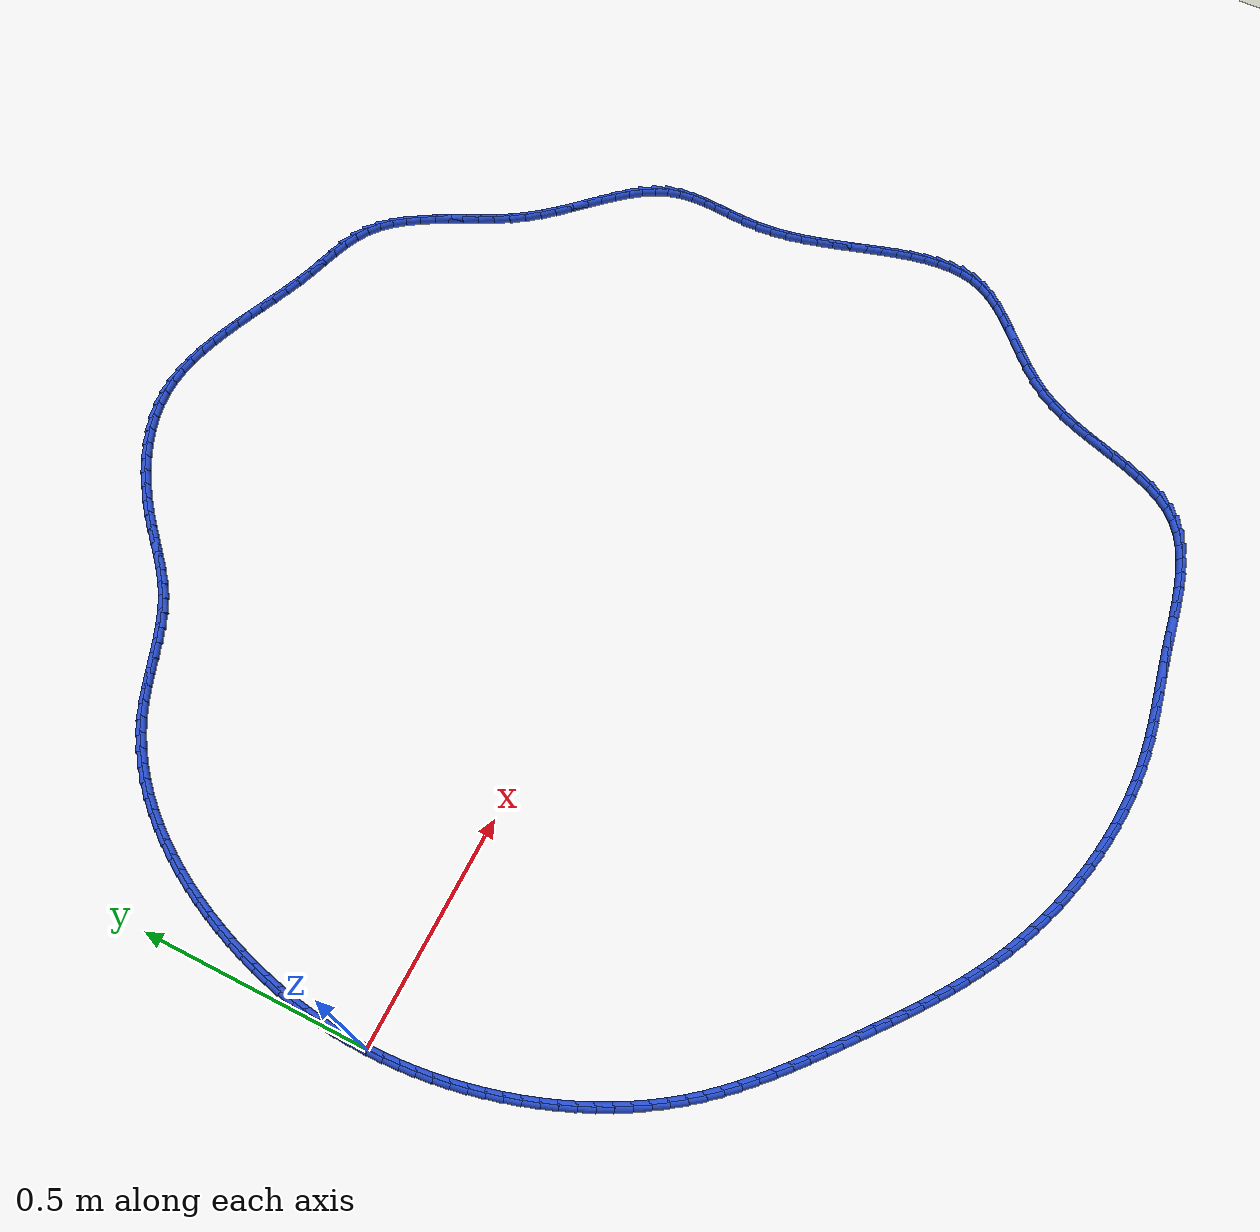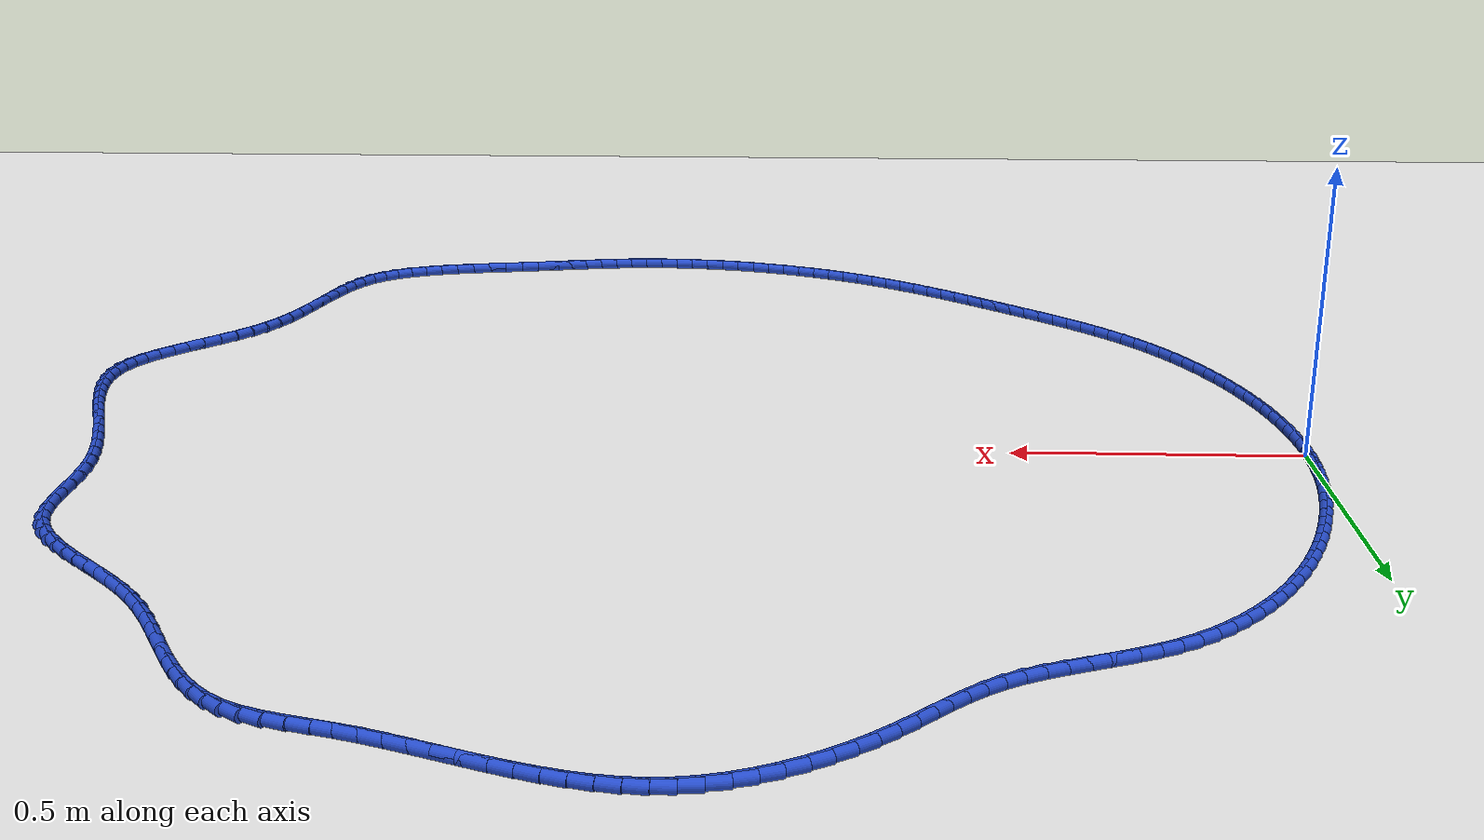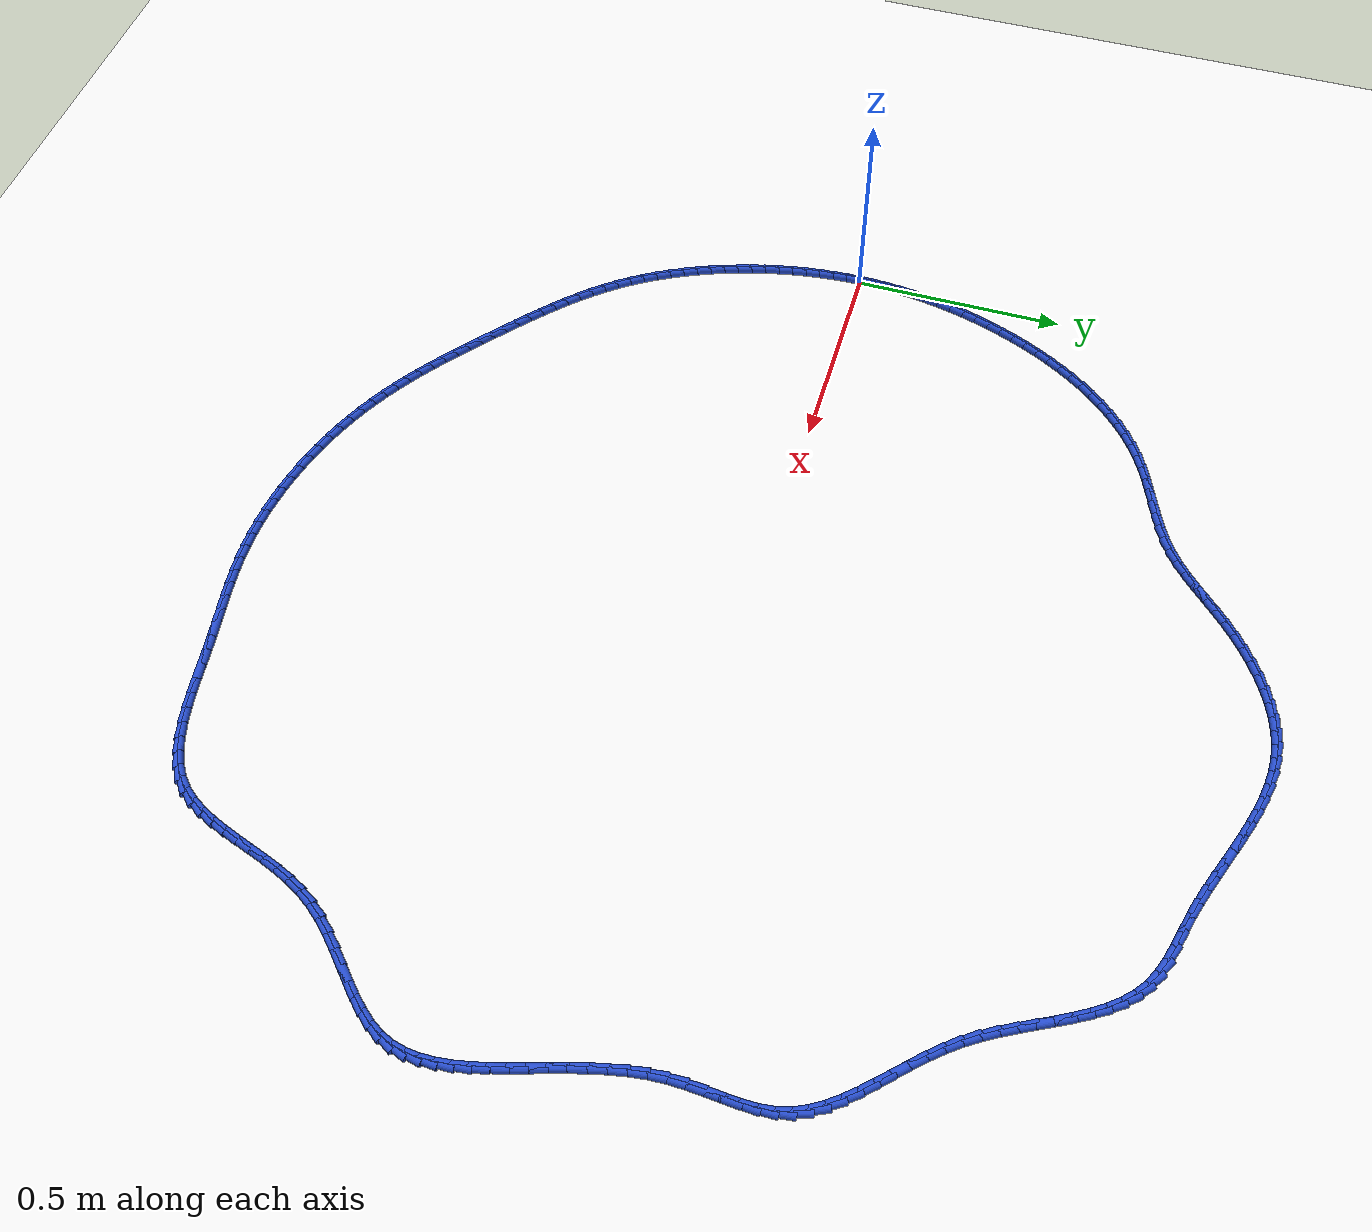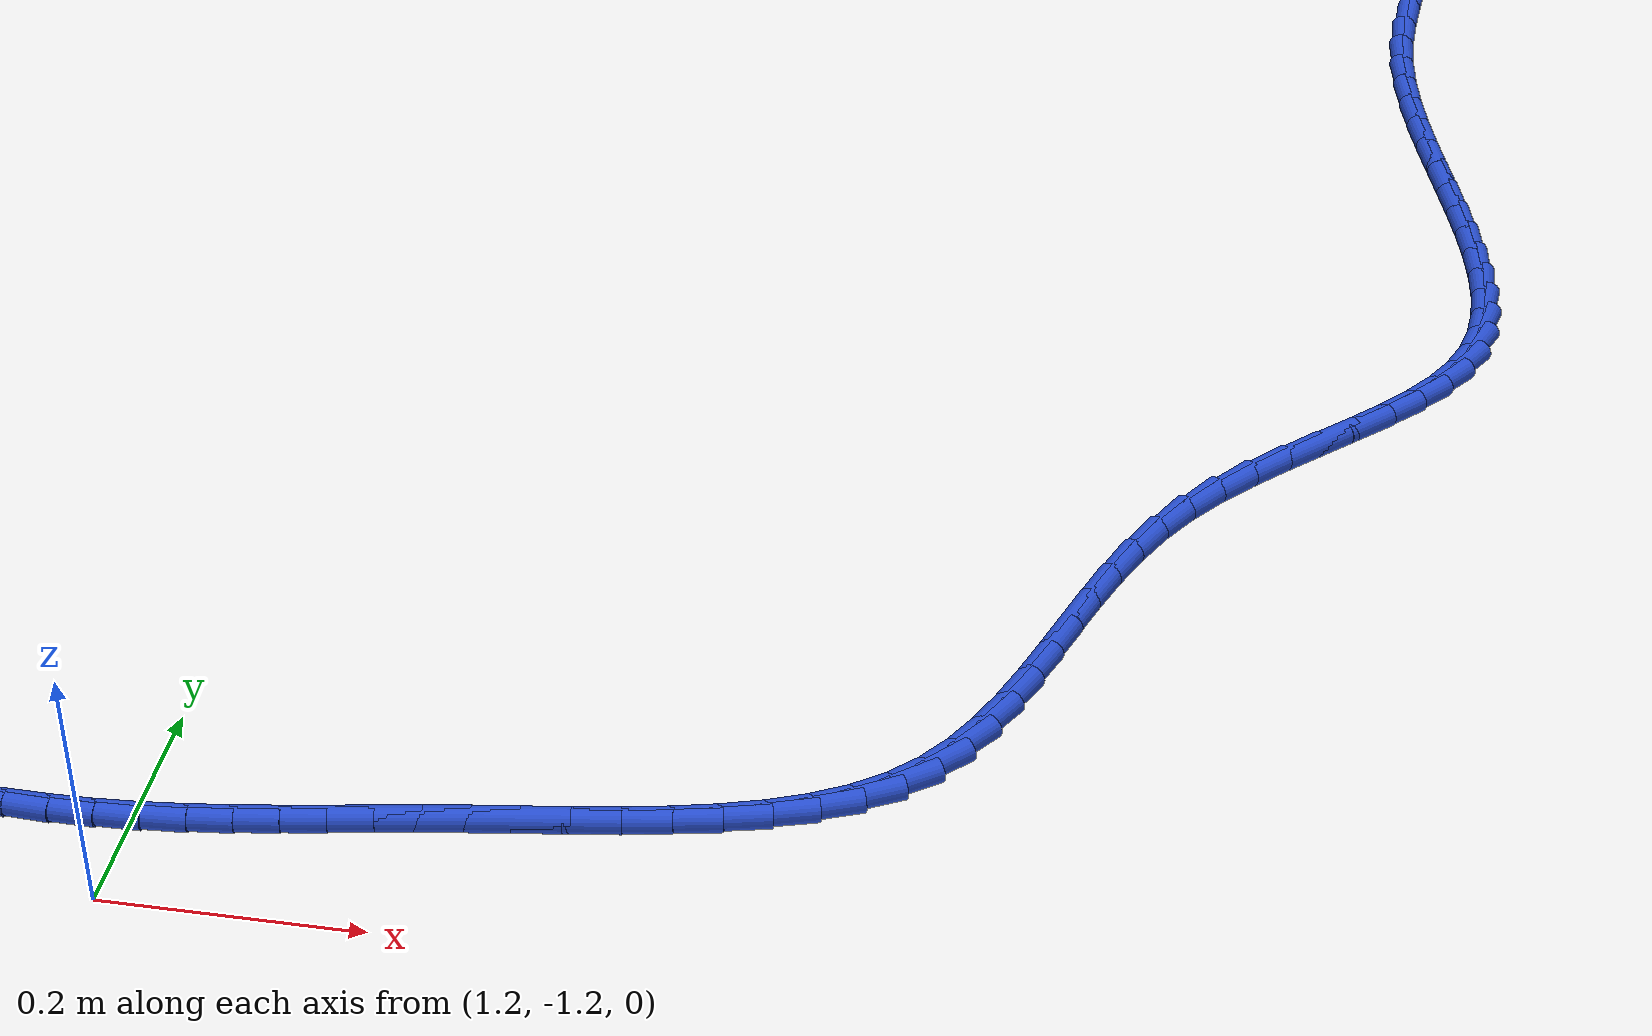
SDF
<sdf version="1.6">
 <world name="default">
  <light name="sun" type="directional">
   <pose>0 0 10 0 -0 0</pose>
   <diffuse>0.8 0.8 0.8 1</diffuse>
   <specular>0.2 0.2 0.2 1</specular>
   <attenuation>
    <range>1000</range>
    <constant>0.9</constant>
    <linear>0.01</linear>
    <quadratic>0.001</quadratic>
   </attenuation>
   <direction>-0.5 0.1 -0.9</direction>
  </light>
  <model name="ground_plane">
   <static>1</static>
   <link name="link">
    <collision name="collision">
     <geometry><plane><normal>0 0 1</normal><size>100 100</size></plane></geometry>
     <surface><friction><ode><mu>100</mu><mu2>50</mu2></ode></friction></surface>
    </collision>
    <visual name="visual">
     <cast_shadows>0</cast_shadows>
     <geometry><plane><normal>0 0 1</normal><size>100 100</size></plane></geometry>
     <material>
      <script><uri>file://media/materials/scripts/gazebo.material</uri><name>Gazebo/WhiteGlow</name></script>
     </material>
    </visual>
   </link>
  </model>
  <gravity>0 0 -9.8</gravity>
  <magnetic_field>6e-06 2.3e-05 -4.2e-05</magnetic_field>
  <atmosphere type="adiabatic"/>
  <physics name="default_physics" default="0" type="ode">
   <max_step_size>0.001</max_step_size>
   <real_time_factor>1</real_time_factor>
   <real_time_update_rate>1000</real_time_update_rate>
  </physics>
  <scene><ambient>0.4 0.4 0.4 1</ambient><background>0.7 0.7 0.7 1</background><shadows>1</shadows></scene>
  <spherical_coordinates>
   <surface_model>EARTH_WGS84</surface_model>
   <latitude_deg>0</latitude_deg>
   <longitude_deg>0</longitude_deg>
   <elevation>0</elevation>
   <heading_deg>0</heading_deg>
  </spherical_coordinates>
  <model name="line">
   <link name="link_0">
    <pose>-2.2551405187698492e-17 6.245004513516506e-17 0.01 0 1.57 1.5546505836131481</pose>
    <collision name="collision">
     <geometry><cylinder><radius>0.01</radius><length>0.08</length></cylinder></geometry>
    </collision>
    <visual name="visual">
     <material>
      <script><name>Gazebo/Blue</name><uri>file://media/materials/scripts/gazebo.material</uri></script>
     </material>
     <geometry><cylinder><radius>0.01</radius><length>0.08</length></cylinder></geometry>
    </visual>
   </link>
   <link name="link_1">
    <pose>0.0005475370954749573 0.03390921744790926 0.01 0 1.57 1.5195633038309866</pose>
    <collision name="collision">
     <geometry><cylinder><radius>0.01</radius><length>0.08</length></cylinder></geometry>
    </collision>
    <visual name="visual">
     <material>
      <script><name>Gazebo/Blue</name><uri>file://media/materials/scripts/gazebo.material</uri></script>
     </material>
     <geometry><cylinder><radius>0.01</radius><length>0.08</length></cylinder></geometry>
    </visual>
   </link>
   <link name="link_2">
    <pose>0.0022830540384516295 0.06775454029161634 0.01 0 1.57 1.484695942037421</pose>
    <collision name="collision">
     <geometry><cylinder><radius>0.01</radius><length>0.08</length></cylinder></geometry>
    </collision>
    <visual name="visual">
     <material>
      <script><name>Gazebo/Blue</name><uri>file://media/materials/scripts/gazebo.material</uri></script>
     </material>
     <geometry><cylinder><radius>0.01</radius><length>0.08</length></cylinder></geometry>
    </visual>
   </link>
   <link name="link_3">
    <pose>0.005199009365725293 0.10153773623996958 0.01 0 1.57 1.4501365469653542</pose>
    <collision name="collision">
     <geometry><cylinder><radius>0.01</radius><length>0.08</length></cylinder></geometry>
    </collision>
    <visual name="visual">
     <material>
      <script><name>Gazebo/Blue</name><uri>file://media/materials/scripts/gazebo.material</uri></script>
     </material>
     <geometry><cylinder><radius>0.01</radius><length>0.08</length></cylinder></geometry>
    </visual>
   </link>
   <link name="link_4">
    <pose>0.009287861614091245 0.13526057300181726 0.01 0 1.57 1.4159686607866893</pose>
    <collision name="collision">
     <geometry><cylinder><radius>0.01</radius><length>0.08</length></cylinder></geometry>
    </collision>
    <visual name="visual">
     <material>
      <script><name>Gazebo/Blue</name><uri>file://media/materials/scripts/gazebo.material</uri></script>
     </material>
     <geometry><cylinder><radius>0.01</radius><length>0.08</length></cylinder></geometry>
    </visual>
   </link>
   <link name="link_5">
    <pose>0.014542069320344787 0.16892481828600792 0.01 0 1.57 1.3822702433500793</pose>
    <collision name="collision">
     <geometry><cylinder><radius>0.01</radius><length>0.08</length></cylinder></geometry>
    </collision>
    <visual name="visual">
     <material>
      <script><name>Gazebo/Blue</name><uri>file://media/materials/scripts/gazebo.material</uri></script>
     </material>
     <geometry><cylinder><radius>0.01</radius><length>0.08</length></cylinder></geometry>
    </visual>
   </link>
   <link name="link_6">
    <pose>0.0209540910212812 0.2025322398013895 0.01 0 1.57 1.3491127902157156</pose>
    <collision name="collision">
     <geometry><cylinder><radius>0.01</radius><length>0.08</length></cylinder></geometry>
    </collision>
    <visual name="visual">
     <material>
      <script><name>Gazebo/Blue</name><uri>file://media/materials/scripts/gazebo.material</uri></script>
     </material>
     <geometry><cylinder><radius>0.01</radius><length>0.08</length></cylinder></geometry>
    </visual>
   </link>
   <link name="link_7">
    <pose>0.02851638525369582 0.23608460525681077 0.01 0 1.57 1.3165606628394473</pose>
    <collision name="collision">
     <geometry><cylinder><radius>0.01</radius><length>0.08</length></cylinder></geometry>
    </collision>
    <visual name="visual">
     <material>
      <script><name>Gazebo/Blue</name><uri>file://media/materials/scripts/gazebo.material</uri></script>
     </material>
     <geometry><cylinder><radius>0.01</radius><length>0.08</length></cylinder></geometry>
    </visual>
   </link>
   <link name="link_8">
    <pose>0.037221410554383896 0.2695836823611198 0.01 0 1.57 1.2846706371338292</pose>
    <collision name="collision">
     <geometry><cylinder><radius>0.01</radius><length>0.08</length></cylinder></geometry>
    </collision>
    <visual name="visual">
     <material>
      <script><name>Gazebo/Blue</name><uri>file://media/materials/scripts/gazebo.material</uri></script>
     </material>
     <geometry><cylinder><radius>0.01</radius><length>0.08</length></cylinder></geometry>
    </visual>
   </link>
   <link name="link_9">
    <pose>0.04706162546014076 0.30303123882316496 0.01 0 1.57 1.2533422447960696</pose>
    <collision name="collision">
     <geometry><cylinder><radius>0.01</radius><length>0.08</length></cylinder></geometry>
    </collision>
    <visual name="visual">
     <material>
      <script><name>Gazebo/Blue</name><uri>file://media/materials/scripts/gazebo.material</uri></script>
     </material>
     <geometry><cylinder><radius>0.01</radius><length>0.08</length></cylinder></geometry>
    </visual>
   </link>
   <link name="link_10">
    <pose>0.05803112161716568 0.3364171857681819 0.01 0 1.57 1.2215018398125381</pose>
    <collision name="collision">
     <geometry><cylinder><radius>0.01</radius><length>0.08</length></cylinder></geometry>
    </collision>
    <visual name="visual">
     <material>
      <script><name>Gazebo/Blue</name><uri>file://media/materials/scripts/gazebo.material</uri></script>
     </material>
     <geometry><cylinder><radius>0.01</radius><length>0.08</length></cylinder></geometry>
    </visual>
   </link>
   <link name="link_11">
    <pose>0.07013528278180435 0.36964945215426603 0.01 0 1.57 1.1885061071895433</pose>
    <collision name="collision">
     <geometry><cylinder><radius>0.01</radius><length>0.08</length></cylinder></geometry>
    </collision>
    <visual name="visual">
     <material>
      <script><name>Gazebo/Blue</name><uri>file://media/materials/scripts/gazebo.material</uri></script>
     </material>
     <geometry><cylinder><radius>0.01</radius><length>0.08</length></cylinder></geometry>
    </visual>
   </link>
   <link name="link_12">
    <pose>0.08338426484035553 0.40260132066433907 0.01 0 1.57 1.1541203871175276</pose>
    <collision name="collision">
     <geometry><cylinder><radius>0.01</radius><length>0.08</length></cylinder></geometry>
    </collision>
    <visual name="visual">
     <material>
      <script><name>Gazebo/Blue</name><uri>file://media/materials/scripts/gazebo.material</uri></script>
     </material>
     <geometry><cylinder><radius>0.01</radius><length>0.08</length></cylinder></geometry>
    </visual>
   </link>
   <link name="link_13">
    <pose>0.09778824064557189 0.4351459508026929 0.01 0 1.57 1.1181077435158975</pose>
    <collision name="collision">
     <geometry><cylinder><radius>0.01</radius><length>0.08</length></cylinder></geometry>
    </collision>
    <visual name="visual">
     <material>
      <script><name>Gazebo/Blue</name><uri>file://media/materials/scripts/gazebo.material</uri></script>
     </material>
     <geometry><cylinder><radius>0.01</radius><length>0.08</length></cylinder></geometry>
    </visual>
   </link>
   <link name="link_14">
    <pose>0.11335738305020596 0.4671565020736193 0.01 0 1.57 1.08022633529933</pose>
    <collision name="collision">
     <geometry><cylinder><radius>0.01</radius><length>0.08</length></cylinder></geometry>
    </collision>
    <visual name="visual">
     <material>
      <script><name>Gazebo/Blue</name><uri>file://media/materials/scripts/gazebo.material</uri></script>
     </material>
     <geometry><cylinder><radius>0.01</radius><length>0.08</length></cylinder></geometry>
    </visual>
   </link>
   <link name="link_15">
    <pose>0.13010186490701037 0.49850613398140997 0.01 0 1.57 1.0402296142396255</pose>
    <collision name="collision">
     <geometry><cylinder><radius>0.01</radius><length>0.08</length></cylinder></geometry>
    </collision>
    <visual name="visual">
     <material>
      <script><name>Gazebo/Blue</name><uri>file://media/materials/scripts/gazebo.material</uri></script>
     </material>
     <geometry><cylinder><radius>0.01</radius><length>0.08</length></cylinder></geometry>
    </visual>
   </link>
   <link name="link_16">
    <pose>0.1480318590687378 0.529068006030357 0.01 0 1.57 0.9978681185886357</pose>
    <collision name="collision">
     <geometry><cylinder><radius>0.01</radius><length>0.08</length></cylinder></geometry>
    </collision>
    <visual name="visual">
     <material>
      <script><name>Gazebo/Blue</name><uri>file://media/materials/scripts/gazebo.material</uri></script>
     </material>
     <geometry><cylinder><radius>0.01</radius><length>0.08</length></cylinder></geometry>
    </visual>
   </link>
   <link name="link_17">
    <pose>0.16715753838814087 0.5587152777247519 0.01 0 1.57 0.9528932970076146</pose>
    <collision name="collision">
     <geometry><cylinder><radius>0.01</radius><length>0.08</length></cylinder></geometry>
    </collision>
    <visual name="visual">
     <material>
      <script><name>Gazebo/Blue</name><uri>file://media/materials/scripts/gazebo.material</uri></script>
     </material>
     <geometry><cylinder><radius>0.01</radius><length>0.08</length></cylinder></geometry>
    </visual>
   </link>
   <link name="link_18">
    <pose>0.18748907571797213 0.5873211085688868 0.01 0 1.57 0.9050638921609957</pose>
    <collision name="collision">
     <geometry><cylinder><radius>0.01</radius><length>0.08</length></cylinder></geometry>
    </collision>
    <visual name="visual">
     <material>
      <script><name>Gazebo/Blue</name><uri>file://media/materials/scripts/gazebo.material</uri></script>
     </material>
     <geometry><cylinder><radius>0.01</radius><length>0.08</length></cylinder></geometry>
    </visual>
   </link>
   <link name="link_19">
    <pose>0.20903664391098428 0.614758658067053 0.01 0 1.57 0.8541554583201467</pose>
    <collision name="collision">
     <geometry><cylinder><radius>0.01</radius><length>0.08</length></cylinder></geometry>
    </collision>
    <visual name="visual">
     <material>
      <script><name>Gazebo/Blue</name><uri>file://media/materials/scripts/gazebo.material</uri></script>
     </material>
     <geometry><cylinder><radius>0.01</radius><length>0.08</length></cylinder></geometry>
    </visual>
   </link>
   <link name="link_20">
    <pose>0.23181041581992992 0.6409010857235428 0.01 0 1.57 0.7999735295833246</pose>
    <collision name="collision">
     <geometry><cylinder><radius>0.01</radius><length>0.08</length></cylinder></geometry>
    </collision>
    <visual name="visual">
     <material>
      <script><name>Gazebo/Blue</name><uri>file://media/materials/scripts/gazebo.material</uri></script>
     </material>
     <geometry><cylinder><radius>0.01</radius><length>0.08</length></cylinder></geometry>
    </visual>
   </link>
   <link name="link_21">
    <pose>0.2558205642975616 0.6656215510426478 0.01 0 1.57 0.7423707199742395</pose>
    <collision name="collision">
     <geometry><cylinder><radius>0.01</radius><length>0.08</length></cylinder></geometry>
    </collision>
    <visual name="visual">
     <material>
      <script><name>Gazebo/Blue</name><uri>file://media/materials/scripts/gazebo.material</uri></script>
     </material>
     <geometry><cylinder><radius>0.01</radius><length>0.08</length></cylinder></geometry>
    </visual>
   </link>
   <link name="link_22">
    <pose>0.28107726219663204 0.6887932135286594 0.01 0 1.57 0.6812675363874473</pose>
    <collision name="collision">
     <geometry><cylinder><radius>0.01</radius><length>0.08</length></cylinder></geometry>
    </collision>
    <visual name="visual">
     <material>
      <script><name>Gazebo/Blue</name><uri>file://media/materials/scripts/gazebo.material</uri></script>
     </material>
     <geometry><cylinder><radius>0.01</radius><length>0.08</length></cylinder></geometry>
    </visual>
   </link>
   <link name="link_23">
    <pose>0.30759068236989384 0.7102892326858703 0.01 0 1.57 0.6166758501954666</pose>
    <collision name="collision">
     <geometry><cylinder><radius>0.01</radius><length>0.08</length></cylinder></geometry>
    </collision>
    <visual name="visual">
     <material>
      <script><name>Gazebo/Blue</name><uri>file://media/materials/scripts/gazebo.material</uri></script>
     </material>
     <geometry><cylinder><radius>0.01</radius><length>0.08</length></cylinder></geometry>
    </visual>
   </link>
   <link name="link_24">
    <pose>0.3353709976700996 0.7299827680185716 0.01 0 1.57 0.5487228091090631</pose>
    <collision name="collision">
     <geometry><cylinder><radius>0.01</radius><length>0.08</length></cylinder></geometry>
    </collision>
    <visual name="visual">
     <material>
      <script><name>Gazebo/Blue</name><uri>file://media/materials/scripts/gazebo.material</uri></script>
     </material>
     <geometry><cylinder><radius>0.01</radius><length>0.08</length></cylinder></geometry>
    </visual>
   </link>
   <link name="link_25">
    <pose>0.36442838095000185 0.7477469790310552 0.01 0 1.57 0.47883147943014925</pose>
    <collision name="collision">
     <geometry><cylinder><radius>0.01</radius><length>0.08</length></cylinder></geometry>
    </collision>
    <visual name="visual">
     <material>
      <script><name>Gazebo/Blue</name><uri>file://media/materials/scripts/gazebo.material</uri></script>
     </material>
     <geometry><cylinder><radius>0.01</radius><length>0.08</length></cylinder></geometry>
    </visual>
   </link>
   <link name="link_26">
    <pose>0.39475342067730923 0.7634895112278638 0.01 0 1.57 0.4215426536250272</pose>
    <collision name="collision">
     <geometry><cylinder><radius>0.01</radius><length>0.08</length></cylinder></geometry>
    </collision>
    <visual name="visual">
     <material>
      <script><name>Gazebo/Blue</name><uri>file://media/materials/scripts/gazebo.material</uri></script>
     </material>
     <geometry><cylinder><radius>0.01</radius><length>0.08</length></cylinder></geometry>
    </visual>
   </link>
   <link name="link_27">
    <pose>0.42609490755866697 0.7775437900208324 0.01 0 1.57 0.3861324462387729</pose>
    <collision name="collision">
     <geometry><cylinder><radius>0.01</radius><length>0.08</length></cylinder></geometry>
    </collision>
    <visual name="visual">
     <material>
      <script><name>Gazebo/Blue</name><uri>file://media/materials/scripts/gazebo.material</uri></script>
     </material>
     <geometry><cylinder><radius>0.01</radius><length>0.08</length></cylinder></geometry>
    </visual>
   </link>
   <link name="link_28">
    <pose>0.45803865148050993 0.7905302325549503 0.01 0 1.57 0.372238912847604</pose>
    <collision name="collision">
     <geometry><cylinder><radius>0.01</radius><length>0.08</length></cylinder></geometry>
    </collision>
    <visual name="visual">
     <material>
      <script><name>Gazebo/Blue</name><uri>file://media/materials/scripts/gazebo.material</uri></script>
     </material>
     <geometry><cylinder><radius>0.01</radius><length>0.08</length></cylinder></geometry>
    </visual>
   </link>
   <link name="link_29">
    <pose>0.49016741432837224 0.8030746231776777 0.01 0 1.57 0.3796819321892362</pose>
    <collision name="collision">
     <geometry><cylinder><radius>0.01</radius><length>0.08</length></cylinder></geometry>
    </collision>
    <visual name="visual">
     <material>
      <script><name>Gazebo/Blue</name><uri>file://media/materials/scripts/gazebo.material</uri></script>
     </material>
     <geometry><cylinder><radius>0.01</radius><length>0.08</length></cylinder></geometry>
    </visual>
   </link>
   <link name="link_30">
    <pose>0.5220639579877888 0.8158027462364752 0.01 0 1.57 0.4088333478817358</pose>
    <collision name="collision">
     <geometry><cylinder><radius>0.01</radius><length>0.08</length></cylinder></geometry>
    </collision>
    <visual name="visual">
     <material>
      <script><name>Gazebo/Blue</name><uri>file://media/materials/scripts/gazebo.material</uri></script>
     </material>
     <geometry><cylinder><radius>0.01</radius><length>0.08</length></cylinder></geometry>
    </visual>
   </link>
   <link name="link_31">
    <pose>0.5533110443442938 0.8293403860788024 0.01 0 1.57 0.46053468392387037</pose>
    <collision name="collision">
     <geometry><cylinder><radius>0.01</radius><length>0.08</length></cylinder></geometry>
    </collision>
    <visual name="visual">
     <material>
      <script><name>Gazebo/Blue</name><uri>file://media/materials/scripts/gazebo.material</uri></script>
     </material>
     <geometry><cylinder><radius>0.01</radius><length>0.08</length></cylinder></geometry>
    </visual>
   </link>
   <link name="link_32">
    <pose>0.5834914352834218 0.8443133270521206 0.01 0 1.57 0.5356910672907709</pose>
    <collision name="collision">
     <geometry><cylinder><radius>0.01</radius><length>0.08</length></cylinder></geometry>
    </collision>
    <visual name="visual">
     <material>
      <script><name>Gazebo/Blue</name><uri>file://media/materials/scripts/gazebo.material</uri></script>
     </material>
     <geometry><cylinder><radius>0.01</radius><length>0.08</length></cylinder></geometry>
    </visual>
   </link>
   <link name="link_33">
    <pose>0.6121879825994719 0.861347238145395 0.01 0 1.57 0.6248551662311486</pose>
    <collision name="collision">
     <geometry><cylinder><radius>0.01</radius><length>0.08</length></cylinder></geometry>
    </collision>
    <visual name="visual">
     <material>
      <script><name>Gazebo/Blue</name><uri>file://media/materials/scripts/gazebo.material</uri></script>
     </material>
     <geometry><cylinder><radius>0.01</radius><length>0.08</length></cylinder></geometry>
    </visual>
   </link>
   <link name="link_34">
    <pose>0.6391800501746308 0.8808156512102565 0.01 0 1.57 0.6968018063996695</pose>
    <collision name="collision">
     <geometry><cylinder><radius>0.01</radius><length>0.08</length></cylinder></geometry>
    </collision>
    <visual name="visual">
     <material>
      <script><name>Gazebo/Blue</name><uri>file://media/materials/scripts/gazebo.material</uri></script>
     </material>
     <geometry><cylinder><radius>0.01</radius><length>0.08</length></cylinder></geometry>
    </visual>
   </link>
   <link name="link_35">
    <pose>0.6648600134872417 0.90230556638586 0.01 0 1.57 0.7449819966224062</pose>
    <collision name="collision">
     <geometry><cylinder><radius>0.01</radius><length>0.08</length></cylinder></geometry>
    </collision>
    <visual name="visual">
     <material>
      <script><name>Gazebo/Blue</name><uri>file://media/materials/scripts/gazebo.material</uri></script>
     </material>
     <geometry><cylinder><radius>0.01</radius><length>0.08</length></cylinder></geometry>
    </visual>
   </link>
   <link name="link_36">
    <pose>0.6897394456837247 0.9252510458464285 0.01 0 1.57 0.769800889194971</pose>
    <collision name="collision">
     <geometry><cylinder><radius>0.01</radius><length>0.08</length></cylinder></geometry>
    </collision>
    <visual name="visual">
     <material>
      <script><name>Gazebo/Blue</name><uri>file://media/materials/scripts/gazebo.material</uri></script>
     </material>
     <geometry><cylinder><radius>0.01</radius><length>0.08</length></cylinder></geometry>
    </visual>
   </link>
   <link name="link_37">
    <pose>0.7143299199105002 0.9490861517661855 0.01 0 1.57 0.7720383358857075</pose>
    <collision name="collision">
     <geometry><cylinder><radius>0.01</radius><length>0.08</length></cylinder></geometry>
    </collision>
    <visual name="visual">
     <material>
      <script><name>Gazebo/Blue</name><uri>file://media/materials/scripts/gazebo.material</uri></script>
     </material>
     <geometry><cylinder><radius>0.01</radius><length>0.08</length></cylinder></geometry>
    </visual>
   </link>
   <link name="link_38">
    <pose>0.7391430093139882 0.9732449463193542 0.01 0 1.57 0.7524419171120212</pose>
    <collision name="collision">
     <geometry><cylinder><radius>0.01</radius><length>0.08</length></cylinder></geometry>
    </collision>
    <visual name="visual">
     <material>
      <script><name>Gazebo/Blue</name><uri>file://media/materials/scripts/gazebo.material</uri></script>
     </material>
     <geometry><cylinder><radius>0.01</radius><length>0.08</length></cylinder></geometry>
    </visual>
   </link>
   <link name="link_39">
    <pose>0.7646902870406087 0.9971614916801576 0.01 0 1.57 0.7125704736528095</pose>
    <collision name="collision">
     <geometry><cylinder><radius>0.01</radius><length>0.08</length></cylinder></geometry>
    </collision>
    <visual name="visual">
     <material>
      <script><name>Gazebo/Blue</name><uri>file://media/materials/scripts/gazebo.material</uri></script>
     </material>
     <geometry><cylinder><radius>0.01</radius><length>0.08</length></cylinder></geometry>
    </visual>
   </link>
   <link name="link_40">
    <pose>0.7914505672919653 1.0202825901623689 0.01 0 1.57 0.6632201292800862</pose>
    <collision name="collision">
     <geometry><cylinder><radius>0.01</radius><length>0.08</length></cylinder></geometry>
    </collision>
    <visual name="visual">
     <material>
      <script><name>Gazebo/Blue</name><uri>file://media/materials/scripts/gazebo.material</uri></script>
     </material>
     <geometry><cylinder><radius>0.01</radius><length>0.08</length></cylinder></geometry>
    </visual>
   </link>
   <link name="link_41">
    <pose>0.8195125270752759 1.0422067706487284 0.01 0 1.57 0.6104533582409338</pose>
    <collision name="collision">
     <geometry><cylinder><radius>0.01</radius><length>0.08</length></cylinder></geometry>
    </collision>
    <visual name="visual">
     <material>
      <script><name>Gazebo/Blue</name><uri>file://media/materials/scripts/gazebo.material</uri></script>
     </material>
     <geometry><cylinder><radius>0.01</radius><length>0.08</length></cylinder></geometry>
    </visual>
   </link>
   <link name="link_42">
    <pose>0.8487086473389942 1.0626321981231703 0.01 0 1.57 0.5532800253266655</pose>
    <collision name="collision">
     <geometry><cylinder><radius>0.01</radius><length>0.08</length></cylinder></geometry>
    </collision>
    <visual name="visual">
     <material>
      <script><name>Gazebo/Blue</name><uri>file://media/materials/scripts/gazebo.material</uri></script>
     </material>
     <geometry><cylinder><radius>0.01</radius><length>0.08</length></cylinder></geometry>
    </visual>
   </link>
   <link name="link_43">
    <pose>0.8788669325456652 1.0812587785004035 0.01 0 1.57 0.4905054897612987</pose>
    <collision name="collision">
     <geometry><cylinder><radius>0.01</radius><length>0.08</length></cylinder></geometry>
    </collision>
    <visual name="visual">
     <material>
      <script><name>Gazebo/Blue</name><uri>file://media/materials/scripts/gazebo.material</uri></script>
     </material>
     <geometry><cylinder><radius>0.01</radius><length>0.08</length></cylinder></geometry>
    </visual>
   </link>
   <link name="link_44">
    <pose>0.9098153871578345 1.0977864176951366 0.01 0 1.57 0.4208399566569972</pose>
    <collision name="collision">
     <geometry><cylinder><radius>0.01</radius><length>0.08</length></cylinder></geometry>
    </collision>
    <visual name="visual">
     <material>
      <script><name>Gazebo/Blue</name><uri>file://media/materials/scripts/gazebo.material</uri></script>
     </material>
     <geometry><cylinder><radius>0.01</radius><length>0.08</length></cylinder></geometry>
    </visual>
   </link>
   <link name="link_45">
    <pose>0.9413820156380472 1.1119150216220777 0.01 0 1.57 0.3429222437895024</pose>
    <collision name="collision">
     <geometry><cylinder><radius>0.01</radius><length>0.08</length></cylinder></geometry>
    </collision>
    <visual name="visual">
     <material>
      <script><name>Gazebo/Blue</name><uri>file://media/materials/scripts/gazebo.material</uri></script>
     </material>
     <geometry><cylinder><radius>0.01</radius><length>0.08</length></cylinder></geometry>
    </visual>
   </link>
   <link name="link_46">
    <pose>0.9733948224488482 1.1233444961959358 0.01 0 1.57 0.255401556500852</pose>
    <collision name="collision">
     <geometry><cylinder><radius>0.01</radius><length>0.08</length></cylinder></geometry>
    </collision>
    <visual name="visual">
     <material>
      <script><name>Gazebo/Blue</name><uri>file://media/materials/scripts/gazebo.material</uri></script>
     </material>
     <geometry><cylinder><radius>0.01</radius><length>0.08</length></cylinder></geometry>
    </visual>
   </link>
   <link name="link_47">
    <pose>1.0056818120527837 1.1317747473314195 0.01 0 1.57 0.15710950941002946</pose>
    <collision name="collision">
     <geometry><cylinder><radius>0.01</radius><length>0.08</length></cylinder></geometry>
    </collision>
    <visual name="visual">
     <material>
      <script><name>Gazebo/Blue</name><uri>file://media/materials/scripts/gazebo.material</uri></script>
     </material>
     <geometry><cylinder><radius>0.01</radius><length>0.08</length></cylinder></geometry>
    </visual>
   </link>
   <link name="link_48">
    <pose>1.0380709889123982 1.136905680943237 0.01 0 1.57 0.050139015077742856</pose>
    <collision name="collision">
     <geometry><cylinder><radius>0.01</radius><length>0.08</length></cylinder></geometry>
    </collision>
    <visual name="visual">
     <material>
      <script><name>Gazebo/Blue</name><uri>file://media/materials/scripts/gazebo.material</uri></script>
     </material>
     <geometry><cylinder><radius>0.01</radius><length>0.08</length></cylinder></geometry>
    </visual>
   </link>
   <link name="link_49">
    <pose>1.0704174960974069 1.1385288633667494 0.01 0 1.57 -0.05053503857043685</pose>
    <collision name="collision">
     <geometry><cylinder><radius>0.01</radius><length>0.08</length></cylinder></geometry>
    </collision>
    <visual name="visual">
     <material>
      <script><name>Gazebo/Blue</name><uri>file://media/materials/scripts/gazebo.material</uri></script>
     </material>
     <geometry><cylinder><radius>0.01</radius><length>0.08</length></cylinder></geometry>
    </visual>
   </link>
   <link name="link_50">
    <pose>1.102712548076787 1.136895440959878 0.01 0 1.57 -0.13837617292794638</pose>
    <collision name="collision">
     <geometry><cylinder><radius>0.01</radius><length>0.08</length></cylinder></geometry>
    </collision>
    <visual name="visual">
     <material>
      <script><name>Gazebo/Blue</name><uri>file://media/materials/scripts/gazebo.material</uri></script>
     </material>
     <geometry><cylinder><radius>0.01</radius><length>0.08</length></cylinder></geometry>
    </visual>
   </link>
   <link name="link_51">
    <pose>1.1349899159255852 1.1324002946646168 0.01 0 1.57 -0.21233384524929502</pose>
    <collision name="collision">
     <geometry><cylinder><radius>0.01</radius><length>0.08</length></cylinder></geometry>
    </collision>
    <visual name="visual">
     <material>
      <script><name>Gazebo/Blue</name><uri>file://media/materials/scripts/gazebo.material</uri></script>
     </material>
     <geometry><cylinder><radius>0.01</radius><length>0.08</length></cylinder></geometry>
    </visual>
   </link>
   <link name="link_52">
    <pose>1.1672833852256324 1.1254383544195048 0.01 0 1.57 -0.27236821823847374</pose>
    <collision name="collision">
     <geometry><cylinder><radius>0.01</radius><length>0.08</length></cylinder></geometry>
    </collision>
    <visual name="visual">
     <material>
      <script><name>Gazebo/Blue</name><uri>file://media/materials/scripts/gazebo.material</uri></script>
     </material>
     <geometry><cylinder><radius>0.01</radius><length>0.08</length></cylinder></geometry>
    </visual>
   </link>
   <link name="link_53">
    <pose>1.1996267415587614 1.1164045501630848 0.01 0 1.57 -0.3190205956463899</pose>
    <collision name="collision">
     <geometry><cylinder><radius>0.01</radius><length>0.08</length></cylinder></geometry>
    </collision>
    <visual name="visual">
     <material>
      <script><name>Gazebo/Blue</name><uri>file://media/materials/scripts/gazebo.material</uri></script>
     </material>
     <geometry><cylinder><radius>0.01</radius><length>0.08</length></cylinder></geometry>
    </visual>
   </link>
   <link name="link_54">
    <pose>1.2320537705068022 1.1056938118338953 0.01 0 1.57 -0.35306257519951395</pose>
    <collision name="collision">
     <geometry><cylinder><radius>0.01</radius><length>0.08</length></cylinder></geometry>
    </collision>
    <visual name="visual">
     <material>
      <script><name>Gazebo/Blue</name><uri>file://media/materials/scripts/gazebo.material</uri></script>
     </material>
     <geometry><cylinder><radius>0.01</radius><length>0.08</length></cylinder></geometry>
    </visual>
   </link>
   <link name="link_55">
    <pose>1.2645982576515873 1.0937010693704774 0.01 0 1.57 -0.3752623566486054</pose>
    <collision name="collision">
     <geometry><cylinder><radius>0.01</radius><length>0.08</length></cylinder></geometry>
    </collision>
    <visual name="visual">
     <material>
      <script><name>Gazebo/Blue</name><uri>file://media/materials/scripts/gazebo.material</uri></script>
     </material>
     <geometry><cylinder><radius>0.01</radius><length>0.08</length></cylinder></geometry>
    </visual>
   </link>
   <link name="link_56">
    <pose>1.2972939885749484 1.080821252711372 0.01 0 1.57 -0.38625204810038843</pose>
    <collision name="collision">
     <geometry><cylinder><radius>0.01</radius><length>0.08</length></cylinder></geometry>
    </collision>
    <visual name="visual">
     <material>
      <script><name>Gazebo/Blue</name><uri>file://media/materials/scripts/gazebo.material</uri></script>
     </material>
     <geometry><cylinder><radius>0.01</radius><length>0.08</length></cylinder></geometry>
    </visual>
   </link>
   <link name="link_57">
    <pose>1.3301747488587168 1.0674492917951197 0.01 0 1.57 -0.38646529747565467</pose>
    <collision name="collision">
     <geometry><cylinder><radius>0.01</radius><length>0.08</length></cylinder></geometry>
    </collision>
    <visual name="visual">
     <material>
      <script><name>Gazebo/Blue</name><uri>file://media/materials/scripts/gazebo.material</uri></script>
     </material>
     <geometry><cylinder><radius>0.01</radius><length>0.08</length></cylinder></geometry>
    </visual>
   </link>
   <link name="link_58">
    <pose>1.3632743240847245 1.0539801165602611 0.01 0 1.57 -0.3761198865224219</pose>
    <collision name="collision">
     <geometry><cylinder><radius>0.01</radius><length>0.08</length></cylinder></geometry>
    </collision>
    <visual name="visual">
     <material>
      <script><name>Gazebo/Blue</name><uri>file://media/materials/scripts/gazebo.material</uri></script>
     </material>
     <geometry><cylinder><radius>0.01</radius><length>0.08</length></cylinder></geometry>
    </visual>
   </link>
   <link name="link_59">
    <pose>1.3966264998348028 1.0408086569453363 0.01 0 1.57 -0.3552306718810577</pose>
    <collision name="collision">
     <geometry><cylinder><radius>0.01</radius><length>0.08</length></cylinder></geometry>
    </collision>
    <visual name="visual">
     <material>
      <script><name>Gazebo/Blue</name><uri>file://media/materials/scripts/gazebo.material</uri></script>
     </material>
     <geometry><cylinder><radius>0.01</radius><length>0.08</length></cylinder></geometry>
    </visual>
   </link>
   <link name="link_60">
    <pose>1.4302650616907833 1.028329842888886 0.01 0 1.57 -0.3236485568408975</pose>
    <collision name="collision">
     <geometry><cylinder><radius>0.01</radius><length>0.08</length></cylinder></geometry>
    </collision>
    <visual name="visual">
     <material>
      <script><name>Gazebo/Blue</name><uri>file://media/materials/scripts/gazebo.material</uri></script>
     </material>
     <geometry><cylinder><radius>0.01</radius><length>0.08</length></cylinder></geometry>
    </visual>
   </link>
   <link name="link_61">
    <pose>1.4642237952344979 1.0169386043294513 0.01 0 1.57 -0.2879294950451845</pose>
    <collision name="collision">
     <geometry><cylinder><radius>0.01</radius><length>0.08</length></cylinder></geometry>
    </collision>
    <visual name="visual">
     <material>
      <script><name>Gazebo/Blue</name><uri>file://media/materials/scripts/gazebo.material</uri></script>
     </material>
     <geometry><cylinder><radius>0.01</radius><length>0.08</length></cylinder></geometry>
    </visual>
   </link>
   <link name="link_62">
    <pose>1.4984207860390664 1.0068108477480653 0.01 0 1.57 -0.2805081604168257</pose>
    <collision name="collision">
     <geometry><cylinder><radius>0.01</radius><length>0.08</length></cylinder></geometry>
    </collision>
    <visual name="visual">
     <material>
      <script><name>Gazebo/Blue</name><uri>file://media/materials/scripts/gazebo.material</uri></script>
     </material>
     <geometry><cylinder><radius>0.01</radius><length>0.08</length></cylinder></geometry>
    </visual>
   </link>
   <link name="link_63">
    <pose>1.5322198276847405 0.9970731888772296 0.01 0 1.57 -0.3125689429357546</pose>
    <collision name="collision">
     <geometry><cylinder><radius>0.01</radius><length>0.08</length></cylinder></geometry>
    </collision>
    <visual name="visual">
     <material>
      <script><name>Gazebo/Blue</name><uri>file://media/materials/scripts/gazebo.material</uri></script>
     </material>
     <geometry><cylinder><radius>0.01</radius><length>0.08</length></cylinder></geometry>
    </visual>
   </link>
   <link name="link_64">
    <pose>1.5648189188030504 0.9865383888239327 0.01 0 1.57 -0.3883813724338014</pose>
    <collision name="collision">
     <geometry><cylinder><radius>0.01</radius><length>0.08</length></cylinder></geometry>
    </collision>
    <visual name="visual">
     <material>
      <script><name>Gazebo/Blue</name><uri>file://media/materials/scripts/gazebo.material</uri></script>
     </material>
     <geometry><cylinder><radius>0.01</radius><length>0.08</length></cylinder></geometry>
    </visual>
   </link>
   <link name="link_65">
    <pose>1.5954160279251 0.9740191517141847 0.01 0 1.57 -0.5135361329263815</pose>
    <collision name="collision">
     <geometry><cylinder><radius>0.01</radius><length>0.08</length></cylinder></geometry>
    </collision>
    <visual name="visual">
     <material>
      <script><name>Gazebo/Blue</name><uri>file://media/materials/scripts/gazebo.material</uri></script>
     </material>
     <geometry><cylinder><radius>0.01</radius><length>0.08</length></cylinder></geometry>
    </visual>
   </link>
   <link name="link_66">
    <pose>1.6232173971291122 0.9583388886276176 0.01 0 1.57 -0.6657670510616024</pose>
    <collision name="collision">
     <geometry><cylinder><radius>0.01</radius><length>0.08</length></cylinder></geometry>
    </collision>
    <visual name="visual">
     <material>
      <script><name>Gazebo/Blue</name><uri>file://media/materials/scripts/gazebo.material</uri></script>
     </material>
     <geometry><cylinder><radius>0.01</radius><length>0.08</length></cylinder></geometry>
    </visual>
   </link>
   <link name="link_67">
    <pose>1.647911200652811 0.9389446881555725 0.01 0 1.57 -0.8008666092819897</pose>
    <collision name="collision">
     <geometry><cylinder><radius>0.01</radius><length>0.08</length></cylinder></geometry>
    </collision>
    <visual name="visual">
     <material>
      <script><name>Gazebo/Blue</name><uri>file://media/materials/scripts/gazebo.material</uri></script>
     </material>
     <geometry><cylinder><radius>0.01</radius><length>0.08</length></cylinder></geometry>
    </visual>
   </link>
   <link name="link_68">
    <pose>1.6699243980751086 0.9162397149556899 0.01 0 1.57 -0.910625793663148</pose>
    <collision name="collision">
     <geometry><cylinder><radius>0.01</radius><length>0.08</length></cylinder></geometry>
    </collision>
    <visual name="visual">
     <material>
      <script><name>Gazebo/Blue</name><uri>file://media/materials/scripts/gazebo.material</uri></script>
     </material>
     <geometry><cylinder><radius>0.01</radius><length>0.08</length></cylinder></geometry>
    </visual>
   </link>
   <link name="link_69">
    <pose>1.6897465504902713 0.8907081474892259 0.01 0 1.57 -0.994356056560531</pose>
    <collision name="collision">
     <geometry><cylinder><radius>0.01</radius><length>0.08</length></cylinder></geometry>
    </collision>
    <visual name="visual">
     <material>
      <script><name>Gazebo/Blue</name><uri>file://media/materials/scripts/gazebo.material</uri></script>
     </material>
     <geometry><cylinder><radius>0.01</radius><length>0.08</length></cylinder></geometry>
    </visual>
   </link>
   <link name="link_70">
    <pose>1.707867218992567 0.8628341642174367 0.01 0 1.57 -1.0537087445718456</pose>
    <collision name="collision">
     <geometry><cylinder><radius>0.01</radius><length>0.08</length></cylinder></geometry>
    </collision>
    <visual name="visual">
     <material>
      <script><name>Gazebo/Blue</name><uri>file://media/materials/scripts/gazebo.material</uri></script>
     </material>
     <geometry><cylinder><radius>0.01</radius><length>0.08</length></cylinder></geometry>
    </visual>
   </link>
   <link name="link_71">
    <pose>1.7247759646762622 0.8331019436015784 0.01 0 1.57 -1.0909957159820505</pose>
    <collision name="collision">
     <geometry><cylinder><radius>0.01</radius><length>0.08</length></cylinder></geometry>
    </collision>
    <visual name="visual">
     <material>
      <script><name>Gazebo/Blue</name><uri>file://media/materials/scripts/gazebo.material</uri></script>
     </material>
     <geometry><cylinder><radius>0.01</radius><length>0.08</length></cylinder></geometry>
    </visual>
   </link>
   <link name="link_72">
    <pose>1.7409623486356243 0.8019956641029067 0.01 0 1.57 -1.1082618858408568</pose>
    <collision name="collision">
     <geometry><cylinder><radius>0.01</radius><length>0.08</length></cylinder></geometry>
    </collision>
    <visual name="visual">
     <material>
      <script><name>Gazebo/Blue</name><uri>file://media/materials/scripts/gazebo.material</uri></script>
     </material>
     <geometry><cylinder><radius>0.01</radius><length>0.08</length></cylinder></geometry>
    </visual>
   </link>
   <link name="link_73">
    <pose>1.7569159319649201 0.769999504182678 0.01 0 1.57 -1.1069163420266026</pose>
    <collision name="collision">
     <geometry><cylinder><radius>0.01</radius><length>0.08</length></cylinder></geometry>
    </collision>
    <visual name="visual">
     <material>
      <script><name>Gazebo/Blue</name><uri>file://media/materials/scripts/gazebo.material</uri></script>
     </material>
     <geometry><cylinder><radius>0.01</radius><length>0.08</length></cylinder></geometry>
    </visual>
   </link>
   <link name="link_74">
    <pose>1.773126275758417 0.7375976423021485 0.01 0 1.57 -1.0876673790786258</pose>
    <collision name="collision">
     <geometry><cylinder><radius>0.01</radius><length>0.08</length></cylinder></geometry>
    </collision>
    <visual name="visual">
     <material>
      <script><name>Gazebo/Blue</name><uri>file://media/materials/scripts/gazebo.material</uri></script>
     </material>
     <geometry><cylinder><radius>0.01</radius><length>0.08</length></cylinder></geometry>
    </visual>
   </link>
   <link name="link_75">
    <pose>1.7900829411103814 0.7052742569225744 0.01 0 1.57 -1.0506169387218292</pose>
    <collision name="collision">
     <geometry><cylinder><radius>0.01</radius><length>0.08</length></cylinder></geometry>
    </collision>
    <visual name="visual">
     <material>
      <script><name>Gazebo/Blue</name><uri>file://media/materials/scripts/gazebo.material</uri></script>
     </material>
     <geometry><cylinder><radius>0.01</radius><length>0.08</length></cylinder></geometry>
    </visual>
   </link>
   <link name="link_76">
    <pose>1.808275489115081 0.6735135265052115 0.01 0 1.57 -0.9954756333079731</pose>
    <collision name="collision">
     <geometry><cylinder><radius>0.01</radius><length>0.08</length></cylinder></geometry>
    </collision>
    <visual name="visual">
     <material>
      <script><name>Gazebo/Blue</name><uri>file://media/materials/scripts/gazebo.material</uri></script>
     </material>
     <geometry><cylinder><radius>0.01</radius><length>0.08</length></cylinder></geometry>
    </visual>
   </link>
   <link name="link_77">
    <pose>1.828193480866782 0.6427996295113163 0.01 0 1.57 -0.9256164374546936</pose>
    <collision name="collision">
     <geometry><cylinder><radius>0.01</radius><length>0.08</length></cylinder></geometry>
    </collision>
    <visual name="visual">
     <material>
      <script><name>Gazebo/Blue</name><uri>file://media/materials/scripts/gazebo.material</uri></script>
     </material>
     <geometry><cylinder><radius>0.01</radius><length>0.08</length></cylinder></geometry>
    </visual>
   </link>
   <link name="link_78">
    <pose>1.8502143167117646 0.6135409751115511 0.01 0 1.57 -0.8658454601131559</pose>
    <collision name="collision">
     <geometry><cylinder><radius>0.01</radius><length>0.08</length></cylinder></geometry>
    </collision>
    <visual name="visual">
     <material>
      <script><name>Gazebo/Blue</name><uri>file://media/materials/scripts/gazebo.material</uri></script>
     </material>
     <geometry><cylinder><radius>0.01</radius><length>0.08</length></cylinder></geometry>
    </visual>
   </link>
   <link name="link_79">
    <pose>1.8739573275378303 0.5856338647551159 0.01 0 1.57 -0.8260537029442379</pose>
    <collision name="collision">
     <geometry><cylinder><radius>0.01</radius><length>0.08</length></cylinder></geometry>
    </collision>
    <visual name="visual">
     <material>
      <script><name>Gazebo/Blue</name><uri>file://media/materials/scripts/gazebo.material</uri></script>
     </material>
     <geometry><cylinder><radius>0.01</radius><length>0.08</length></cylinder></geometry>
    </visual>
   </link>
   <link name="link_80">
    <pose>1.898727951677734 0.5587625523019674 0.01 0 1.57 -0.80586695330066</pose>
    <collision name="collision">
     <geometry><cylinder><radius>0.01</radius><length>0.08</length></cylinder></geometry>
    </collision>
    <visual name="visual">
     <material>
      <script><name>Gazebo/Blue</name><uri>file://media/materials/scripts/gazebo.material</uri></script>
     </material>
     <geometry><cylinder><radius>0.01</radius><length>0.08</length></cylinder></geometry>
    </visual>
   </link>
   <link name="link_81">
    <pose>1.9238306239085943 0.5326106136681296 0.01 0 1.57 -0.8053969014875142</pose>
    <collision name="collision">
     <geometry><cylinder><radius>0.01</radius><length>0.08</length></cylinder></geometry>
    </collision>
    <visual name="visual">
     <material>
      <script><name>Gazebo/Blue</name><uri>file://media/materials/scripts/gazebo.material</uri></script>
     </material>
     <geometry><cylinder><radius>0.01</radius><length>0.08</length></cylinder></geometry>
    </visual>
   </link>
   <link name="link_82">
    <pose>1.9485697790075325 0.506861624769627 0.01 0 1.57 -0.8255526647911544</pose>
    <collision name="collision">
     <geometry><cylinder><radius>0.01</radius><length>0.08</length></cylinder></geometry>
    </collision>
    <visual name="visual">
     <material>
      <script><name>Gazebo/Blue</name><uri>file://media/materials/scripts/gazebo.material</uri></script>
     </material>
     <geometry><cylinder><radius>0.01</radius><length>0.08</length></cylinder></geometry>
    </visual>
   </link>
   <link name="link_83">
    <pose>1.9722498517516673 0.48119916152248415 0.01 0 1.57 -0.8681680627093928</pose>
    <collision name="collision">
     <geometry><cylinder><radius>0.01</radius><length>0.08</length></cylinder></geometry>
    </collision>
    <visual name="visual">
     <material>
      <script><name>Gazebo/Blue</name><uri>file://media/materials/scripts/gazebo.material</uri></script>
     </material>
     <geometry><cylinder><radius>0.01</radius><length>0.08</length></cylinder></geometry>
    </visual>
   </link>
   <link name="link_84">
    <pose>1.9941752769181185 0.45530679984272565 0.01 0 1.57 -0.9359148114598306</pose>
    <collision name="collision">
     <geometry><cylinder><radius>0.01</radius><length>0.08</length></cylinder></geometry>
    </collision>
    <visual name="visual">
     <material>
      <script><name>Gazebo/Blue</name><uri>file://media/materials/scripts/gazebo.material</uri></script>
     </material>
     <geometry><cylinder><radius>0.01</radius><length>0.08</length></cylinder></geometry>
    </visual>
   </link>
   <link name="link_85">
    <pose>2.013650489284007 0.4288681156463754 0.01 0 1.57 -1.031762954885597</pose>
    <collision name="collision">
     <geometry><cylinder><radius>0.01</radius><length>0.08</length></cylinder></geometry>
    </collision>
    <visual name="visual">
     <material>
      <script><name>Gazebo/Blue</name><uri>file://media/materials/scripts/gazebo.material</uri></script>
     </material>
     <geometry><cylinder><radius>0.01</radius><length>0.08</length></cylinder></geometry>
    </visual>
   </link>
   <link name="link_86">
    <pose>2.0299799236264517 0.40156668484945823 0.01 0 1.57 -1.1575660694457235</pose>
    <collision name="collision">
     <geometry><cylinder><radius>0.01</radius><length>0.08</length></cylinder></geometry>
    </collision>
    <visual name="visual">
     <material>
      <script><name>Gazebo/Blue</name><uri>file://media/materials/scripts/gazebo.material</uri></script>
     </material>
     <geometry><cylinder><radius>0.01</radius><length>0.08</length></cylinder></geometry>
    </visual>
   </link>
   <link name="link_87">
    <pose>2.042468014722573 0.3730860833679984 0.01 0 1.57 -1.3108900914198236</pose>
    <collision name="collision">
     <geometry><cylinder><radius>0.01</radius><length>0.08</length></cylinder></geometry>
    </collision>
    <visual name="visual">
     <material>
      <script><name>Gazebo/Blue</name><uri>file://media/materials/scripts/gazebo.material</uri></script>
     </material>
     <geometry><cylinder><radius>0.01</radius><length>0.08</length></cylinder></geometry>
    </visual>
   </link>
   <link name="link_88">
    <pose>2.050437908879543 0.343115190367679 0.01 0 1.57 -1.4586157774025306</pose>
    <collision name="collision">
     <geometry><cylinder><radius>0.01</radius><length>0.08</length></cylinder></geometry>
    </collision>
    <visual name="visual">
     <material>
      <script><name>Gazebo/Blue</name><uri>file://media/materials/scripts/gazebo.material</uri></script>
     </material>
     <geometry><cylinder><radius>0.01</radius><length>0.08</length></cylinder></geometry>
    </visual>
   </link>
   <link name="link_89">
    <pose>2.0539922814052844 0.311563820282199 0.01 0 1.57 -1.56212899563433</pose>
    <collision name="collision">
     <geometry><cylinder><radius>0.01</radius><length>0.08</length></cylinder></geometry>
    </collision>
    <visual name="visual">
     <material>
      <script><name>Gazebo/Blue</name><uri>file://media/materials/scripts/gazebo.material</uri></script>
     </material>
     <geometry><cylinder><radius>0.01</radius><length>0.08</length></cylinder></geometry>
    </visual>
   </link>
   <link name="link_90">
    <pose>2.054277670653478 0.2786376407611913 0.01 0 1.57 1.5190720176206476</pose>
    <collision name="collision">
     <geometry><cylinder><radius>0.01</radius><length>0.08</length></cylinder></geometry>
    </collision>
    <visual name="visual">
     <material>
      <script><name>Gazebo/Blue</name><uri>file://media/materials/scripts/gazebo.material</uri></script>
     </material>
     <geometry><cylinder><radius>0.01</radius><length>0.08</length></cylinder></geometry>
    </visual>
   </link>
   <link name="link_91">
    <pose>2.052513610336646 0.24456300790738608 0.01 0 1.57 1.4968110872426859</pose>
    <collision name="collision">
     <geometry><cylinder><radius>0.01</radius><length>0.08</length></cylinder></geometry>
    </collision>
    <visual name="visual">
     <material>
      <script><name>Gazebo/Blue</name><uri>file://media/materials/scripts/gazebo.material</uri></script>
     </material>
     <geometry><cylinder><radius>0.01</radius><length>0.08</length></cylinder></geometry>
    </visual>
   </link>
   <link name="link_92">
    <pose>2.0499196341673116 0.20956627782351353 0.01 0 1.57 1.5091149144256064</pose>
    <collision name="collision">
     <geometry><cylinder><radius>0.01</radius><length>0.08</length></cylinder></geometry>
    </collision>
    <visual name="visual">
     <material>
      <script><name>Gazebo/Blue</name><uri>file://media/materials/scripts/gazebo.material</uri></script>
     </material>
     <geometry><cylinder><radius>0.01</radius><length>0.08</length></cylinder></geometry>
    </visual>
   </link>
   <link name="link_93">
    <pose>2.0477152758579975 0.17387380661230392 0.01 0 1.57 1.5543382945707942</pose>
    <collision name="collision">
     <geometry><cylinder><radius>0.01</radius><length>0.08</length></cylinder></geometry>
    </collision>
    <visual name="visual">
     <material>
      <script><name>Gazebo/Blue</name><uri>file://media/materials/scripts/gazebo.material</uri></script>
     </material>
     <geometry><cylinder><radius>0.01</radius><length>0.08</length></cylinder></geometry>
    </visual>
   </link>
   <link name="link_94">
    <pose>2.0471200691212283 0.13771195037648745 0.01 0 1.57 -1.5132111645813813</pose>
    <collision name="collision">
     <geometry><cylinder><radius>0.01</radius><length>0.08</length></cylinder></geometry>
    </collision>
    <visual name="visual">
     <material>
      <script><name>Gazebo/Blue</name><uri>file://media/materials/scripts/gazebo.material</uri></script>
     </material>
     <geometry><cylinder><radius>0.01</radius><length>0.08</length></cylinder></geometry>
    </visual>
   </link>
   <link name="link_95">
    <pose>2.0492193242827117 0.10129746172322959 0.01 0 1.57 -1.4400393599211647</pose>
    <collision name="collision">
     <geometry><cylinder><radius>0.01</radius><length>0.08</length></cylinder></geometry>
    </collision>
    <visual name="visual">
     <material>
      <script><name>Gazebo/Blue</name><uri>file://media/materials/scripts/gazebo.material</uri></script>
     </material>
     <geometry><cylinder><radius>0.01</radius><length>0.08</length></cylinder></geometry>
    </visual>
   </link>
   <link name="link_96">
    <pose>2.0540229325984205 0.06477014852963475 0.01 0 1.57 -1.3814746424726665</pose>
    <collision name="collision">
     <geometry><cylinder><radius>0.01</radius><length>0.08</length></cylinder></geometry>
    </collision>
    <visual name="visual">
     <material>
      <script><name>Gazebo/Blue</name><uri>file://media/materials/scripts/gazebo.material</uri></script>
     </material>
     <geometry><cylinder><radius>0.01</radius><length>0.08</length></cylinder></geometry>
    </visual>
   </link>
   <link name="link_97">
    <pose>2.061024082892148 0.02823284933658626 0.01 0 1.57 -1.3367598555480629</pose>
    <collision name="collision">
     <geometry><cylinder><radius>0.01</radius><length>0.08</length></cylinder></geometry>
    </collision>
    <visual name="visual">
     <material>
      <script><name>Gazebo/Blue</name><uri>file://media/materials/scripts/gazebo.material</uri></script>
     </material>
     <geometry><cylinder><radius>0.01</radius><length>0.08</length></cylinder></geometry>
    </visual>
   </link>
   <link name="link_98">
    <pose>2.069712683586535 -0.008211832023144799 0.01 0 1.57 -1.3050644797254614</pose>
    <collision name="collision">
     <geometry><cylinder><radius>0.01</radius><length>0.08</length></cylinder></geometry>
    </collision>
    <visual name="visual">
     <material>
      <script><name>Gazebo/Blue</name><uri>file://media/materials/scripts/gazebo.material</uri></script>
     </material>
     <geometry><cylinder><radius>0.01</radius><length>0.08</length></cylinder></geometry>
    </visual>
   </link>
   <link name="link_99">
    <pose>2.079578643104222 -0.04446129171678792 0.01 0 1.57 -1.2857892807922395</pose>
    <collision name="collision">
     <geometry><cylinder><radius>0.01</radius><length>0.08</length></cylinder></geometry>
    </collision>
    <visual name="visual">
     <material>
      <script><name>Gazebo/Blue</name><uri>file://media/materials/scripts/gazebo.material</uri></script>
     </material>
     <geometry><cylinder><radius>0.01</radius><length>0.08</length></cylinder></geometry>
    </visual>
   </link>
   <link name="link_100">
    <pose>2.09011186986785 -0.08041292591157234 0.01 0 1.57 -1.2786934525549167</pose>
    <collision name="collision">
     <geometry><cylinder><radius>0.01</radius><length>0.08</length></cylinder></geometry>
    </collision>
    <visual name="visual">
     <material>
      <script><name>Gazebo/Blue</name><uri>file://media/materials/scripts/gazebo.material</uri></script>
     </material>
     <geometry><cylinder><radius>0.01</radius><length>0.08</length></cylinder></geometry>
    </visual>
   </link>
   <link name="link_101">
    <pose>2.1008022723000597 -0.11596413077472753 0.01 0 1.57 -1.283978232663764</pose>
    <collision name="collision">
     <geometry><cylinder><radius>0.01</radius><length>0.08</length></cylinder></geometry>
    </collision>
    <visual name="visual">
     <material>
      <script><name>Gazebo/Blue</name><uri>file://media/materials/scripts/gazebo.material</uri></script>
     </material>
     <geometry><cylinder><radius>0.01</radius><length>0.08</length></cylinder></geometry>
    </visual>
   </link>
   <link name="link_102">
    <pose>2.111139758823493 -0.15101230247348277 0.01 0 1.57 -1.3023550243018276</pose>
    <collision name="collision">
     <geometry><cylinder><radius>0.01</radius><length>0.08</length></cylinder></geometry>
    </collision>
    <visual name="visual">
     <material>
      <script><name>Gazebo/Blue</name><uri>file://media/materials/scripts/gazebo.material</uri></script>
     </material>
     <geometry><cylinder><radius>0.01</radius><length>0.08</length></cylinder></geometry>
    </visual>
   </link>
   <link name="link_103">
    <pose>2.1206142378607895 -0.1854548371750675 0.01 0 1.57 -1.335107017514242</pose>
    <collision name="collision">
     <geometry><cylinder><radius>0.01</radius><length>0.08</length></cylinder></geometry>
    </collision>
    <visual name="visual">
     <material>
      <script><name>Gazebo/Blue</name><uri>file://media/materials/scripts/gazebo.material</uri></script>
     </material>
     <geometry><cylinder><radius>0.01</radius><length>0.08</length></cylinder></geometry>
    </visual>
   </link>
   <link name="link_104">
    <pose>2.1287156178345907 -0.21918913104671106 0.01 0 1.57 -1.3841270677325213</pose>
    <collision name="collision">
     <geometry><cylinder><radius>0.01</radius><length>0.08</length></cylinder></geometry>
    </collision>
    <visual name="visual">
     <material>
      <script><name>Gazebo/Blue</name><uri>file://media/materials/scripts/gazebo.material</uri></script>
     </material>
     <geometry><cylinder><radius>0.01</radius><length>0.08</length></cylinder></geometry>
    </visual>
   </link>
   <link name="link_105">
    <pose>2.1349338071675388 -0.2521125802556429 0.01 0 1.57 -1.4518692017173862</pose>
    <collision name="collision">
     <geometry><cylinder><radius>0.01</radius><length>0.08</length></cylinder></geometry>
    </collision>
    <visual name="visual">
     <material>
      <script><name>Gazebo/Blue</name><uri>file://media/materials/scripts/gazebo.material</uri></script>
     </material>
     <geometry><cylinder><radius>0.01</radius><length>0.08</length></cylinder></geometry>
    </visual>
   </link>
   <link name="link_106">
    <pose>2.1387587142822726 -0.2841225809690924 0.01 0 1.57 -1.5410723982234753</pose>
    <collision name="collision">
     <geometry><cylinder><radius>0.01</radius><length>0.08</length></cylinder></geometry>
    </collision>
    <visual name="visual">
     <material>
      <script><name>Gazebo/Blue</name><uri>file://media/materials/scripts/gazebo.material</uri></script>
     </material>
     <geometry><cylinder><radius>0.01</radius><length>0.08</length></cylinder></geometry>
    </visual>
   </link>
   <link name="link_107">
    <pose>2.1396802476014343 -0.3151165293542887 0.01 0 1.57 1.4875778296060802</pose>
    <collision name="collision">
     <geometry><cylinder><radius>0.01</radius><length>0.08</length></cylinder></geometry>
    </collision>
    <visual name="visual">
     <material>
      <script><name>Gazebo/Blue</name><uri>file://media/materials/scripts/gazebo.material</uri></script>
     </material>
     <geometry><cylinder><radius>0.01</radius><length>0.08</length></cylinder></geometry>
    </visual>
   </link>
   <link name="link_108">
    <pose>2.1371883155476645 -0.3449918215784614 0.01 0 1.57 1.3505340721016188</pose>
    <collision name="collision">
     <geometry><cylinder><radius>0.01</radius><length>0.08</length></cylinder></geometry>
    </collision>
    <visual name="visual">
     <material>
      <script><name>Gazebo/Blue</name><uri>file://media/materials/scripts/gazebo.material</uri></script>
     </material>
     <geometry><cylinder><radius>0.01</radius><length>0.08</length></cylinder></geometry>
    </visual>
   </link>
   <link name="link_109">
    <pose>2.1307728265436046 -0.37364585380883997 0.01 0 1.57 1.193020575264305</pose>
    <collision name="collision">
     <geometry><cylinder><radius>0.01</radius><length>0.08</length></cylinder></geometry>
    </collision>
    <visual name="visual">
     <material>
      <script><name>Gazebo/Blue</name><uri>file://media/materials/scripts/gazebo.material</uri></script>
     </material>
     <geometry><cylinder><radius>0.01</radius><length>0.08</length></cylinder></geometry>
    </visual>
   </link>
   <link name="link_110">
    <pose>2.119926809399979 -0.4009770920630132 0.01 0 1.57 1.0378330119150283</pose>
    <collision name="collision">
     <geometry><cylinder><radius>0.01</radius><length>0.08</length></cylinder></geometry>
    </collision>
    <visual name="visual">
     <material>
      <script><name>Gazebo/Blue</name><uri>file://media/materials/scripts/gazebo.material</uri></script>
     </material>
     <geometry><cylinder><radius>0.01</radius><length>0.08</length></cylinder></geometry>
    </visual>
   </link>
   <link name="link_111">
    <pose>2.104559937005867 -0.42702685215961445 0.01 0 1.57 0.9190317664332098</pose>
    <collision name="collision">
     <geometry><cylinder><radius>0.01</radius><length>0.08</length></cylinder></geometry>
    </collision>
    <visual name="visual">
     <material>
      <script><name>Gazebo/Blue</name><uri>file://media/materials/scripts/gazebo.material</uri></script>
     </material>
     <geometry><cylinder><radius>0.01</radius><length>0.08</length></cylinder></geometry>
    </visual>
   </link>
   <link name="link_112">
    <pose>2.0854129858076838 -0.45212140051175703 0.01 0 1.57 0.8371213687278565</pose>
    <collision name="collision">
     <geometry><cylinder><radius>0.01</radius><length>0.08</length></cylinder></geometry>
    </collision>
    <visual name="visual">
     <material>
      <script><name>Gazebo/Blue</name><uri>file://media/materials/scripts/gazebo.material</uri></script>
     </material>
     <geometry><cylinder><radius>0.01</radius><length>0.08</length></cylinder></geometry>
    </visual>
   </link>
   <link name="link_113">
    <pose>2.0633253526186333 -0.4766208163250703 0.01 0 1.57 0.7869552107450904</pose>
    <collision name="collision">
     <geometry><cylinder><radius>0.01</radius><length>0.08</length></cylinder></geometry>
    </collision>
    <visual name="visual">
     <material>
      <script><name>Gazebo/Blue</name><uri>file://media/materials/scripts/gazebo.material</uri></script>
     </material>
     <geometry><cylinder><radius>0.01</radius><length>0.08</length></cylinder></geometry>
    </visual>
   </link>
   <link name="link_114">
    <pose>2.0391364342519163 -0.5008851788051832 0.01 0 1.57 0.7641049490357975</pose>
    <collision name="collision">
     <geometry><cylinder><radius>0.01</radius><length>0.08</length></cylinder></geometry>
    </collision>
    <visual name="visual">
     <material>
      <script><name>Gazebo/Blue</name><uri>file://media/materials/scripts/gazebo.material</uri></script>
     </material>
     <geometry><cylinder><radius>0.01</radius><length>0.08</length></cylinder></geometry>
    </visual>
   </link>
   <link name="link_115">
    <pose>2.0136856275207373 -0.5252745671577254 0.01 0 1.57 0.7657189639922186</pose>
    <collision name="collision">
     <geometry><cylinder><radius>0.01</radius><length>0.08</length></cylinder></geometry>
    </collision>
    <visual name="visual">
     <material>
      <script><name>Gazebo/Blue</name><uri>file://media/materials/scripts/gazebo.material</uri></script>
     </material>
     <geometry><cylinder><radius>0.01</radius><length>0.08</length></cylinder></geometry>
    </visual>
   </link>
   <link name="link_116">
    <pose>1.987812329238298 -0.5501490605883252 0.01 0 1.57 0.7905428016472054</pose>
    <collision name="collision">
     <geometry><cylinder><radius>0.01</radius><length>0.08</length></cylinder></geometry>
    </collision>
    <visual name="visual">
     <material>
      <script><name>Gazebo/Blue</name><uri>file://media/materials/scripts/gazebo.material</uri></script>
     </material>
     <geometry><cylinder><radius>0.01</radius><length>0.08</length></cylinder></geometry>
    </visual>
   </link>
   <link name="link_117">
    <pose>1.9623559362178007 -0.5758687383026131 0.01 0 1.57 0.8386455534718995</pose>
    <collision name="collision">
     <geometry><cylinder><radius>0.01</radius><length>0.08</length></cylinder></geometry>
    </collision>
    <visual name="visual">
     <material>
      <script><name>Gazebo/Blue</name><uri>file://media/materials/scripts/gazebo.material</uri></script>
     </material>
     <geometry><cylinder><radius>0.01</radius><length>0.08</length></cylinder></geometry>
    </visual>
   </link>
   <link name="link_118">
    <pose>1.9381558452724477 -0.6027936795062174 0.01 0 1.57 0.9109509362903813</pose>
    <collision name="collision">
     <geometry><cylinder><radius>0.01</radius><length>0.08</length></cylinder></geometry>
    </collision>
    <visual name="visual">
     <material>
      <script><name>Gazebo/Blue</name><uri>file://media/materials/scripts/gazebo.material</uri></script>
     </material>
     <geometry><cylinder><radius>0.01</radius><length>0.08</length></cylinder></geometry>
    </visual>
   </link>
   <link name="link_119">
    <pose>1.9160514532154422 -0.6312839634047678 0.01 0 1.57 1.006010213123128</pose>
    <collision name="collision">
     <geometry><cylinder><radius>0.01</radius><length>0.08</length></cylinder></geometry>
    </collision>
    <visual name="visual">
     <material>
      <script><name>Gazebo/Blue</name><uri>file://media/materials/scripts/gazebo.material</uri></script>
     </material>
     <geometry><cylinder><radius>0.01</radius><length>0.08</length></cylinder></geometry>
    </visual>
   </link>
   <link name="link_120">
    <pose>1.8968072639399138 -0.661654962181499 0.01 0 1.57 1.0966771953109773</pose>
    <collision name="collision">
     <geometry><cylinder><radius>0.01</radius><length>0.08</length></cylinder></geometry>
    </collision>
    <visual name="visual">
     <material>
      <script><name>Gazebo/Blue</name><uri>file://media/materials/scripts/gazebo.material</uri></script>
     </material>
     <geometry><cylinder><radius>0.01</radius><length>0.08</length></cylinder></geometry>
    </visual>
   </link>
   <link name="link_121">
    <pose>1.8803513884758456 -0.6937227667200658 0.01 0 1.57 1.1657647009384213</pose>
    <collision name="collision">
     <geometry><cylinder><radius>0.01</radius><length>0.08</length></cylinder></geometry>
    </collision>
    <visual name="visual">
     <material>
      <script><name>Gazebo/Blue</name><uri>file://media/materials/scripts/gazebo.material</uri></script>
     </material>
     <geometry><cylinder><radius>0.01</radius><length>0.08</length></cylinder></geometry>
    </visual>
   </link>
   <link name="link_122">
    <pose>1.8660881540754102 -0.7269907973197526 0.01 0 1.57 1.2136596072903987</pose>
    <collision name="collision">
     <geometry><cylinder><radius>0.01</radius><length>0.08</length></cylinder></geometry>
    </collision>
    <visual name="visual">
     <material>
      <script><name>Gazebo/Blue</name><uri>file://media/materials/scripts/gazebo.material</uri></script>
     </material>
     <geometry><cylinder><radius>0.01</radius><length>0.08</length></cylinder></geometry>
    </visual>
   </link>
   <link name="link_123">
    <pose>1.853413842453685 -0.760957671529373 0.01 0 1.57 1.2411376406779047</pose>
    <collision name="collision">
     <geometry><cylinder><radius>0.01</radius><length>0.08</length></cylinder></geometry>
    </collision>
    <visual name="visual">
     <material>
      <script><name>Gazebo/Blue</name><uri>file://media/materials/scripts/gazebo.material</uri></script>
     </material>
     <geometry><cylinder><radius>0.01</radius><length>0.08</length></cylinder></geometry>
    </visual>
   </link>
   <link name="link_124">
    <pose>1.8417247353257475 -0.7951220068977409 0.01 0 1.57 1.248492585191122</pose>
    <collision name="collision">
     <geometry><cylinder><radius>0.01</radius><length>0.08</length></cylinder></geometry>
    </collision>
    <visual name="visual">
     <material>
      <script><name>Gazebo/Blue</name><uri>file://media/materials/scripts/gazebo.material</uri></script>
     </material>
     <geometry><cylinder><radius>0.01</radius><length>0.08</length></cylinder></geometry>
    </visual>
   </link>
   <link name="link_125">
    <pose>1.8304171144066743 -0.8289824209736699 0.01 0 1.57 1.2351847323232221</pose>
    <collision name="collision">
     <geometry><cylinder><radius>0.01</radius><length>0.08</length></cylinder></geometry>
    </collision>
    <visual name="visual">
     <material>
      <script><name>Gazebo/Blue</name><uri>file://media/materials/scripts/gazebo.material</uri></script>
     </material>
     <geometry><cylinder><radius>0.01</radius><length>0.08</length></cylinder></geometry>
    </visual>
   </link>
   <link name="link_126">
    <pose>1.818887261411543 -0.8620375313059738 0.01 0 1.57 1.1996535168013691</pose>
    <collision name="collision">
     <geometry><cylinder><radius>0.01</radius><length>0.08</length></cylinder></geometry>
    </collision>
    <visual name="visual">
     <material>
      <script><name>Gazebo/Blue</name><uri>file://media/materials/scripts/gazebo.material</uri></script>
     </material>
     <geometry><cylinder><radius>0.01</radius><length>0.08</length></cylinder></geometry>
    </visual>
   </link>
   <link name="link_127">
    <pose>1.8065314580554306 -0.893785955443466 0.01 0 1.57 1.1393018010624911</pose>
    <collision name="collision">
     <geometry><cylinder><radius>0.01</radius><length>0.08</length></cylinder></geometry>
    </collision>
    <visual name="visual">
     <material>
      <script><name>Gazebo/Blue</name><uri>file://media/materials/scripts/gazebo.material</uri></script>
     </material>
     <geometry><cylinder><radius>0.01</radius><length>0.08</length></cylinder></geometry>
    </visual>
   </link>
   <link name="link_128">
    <pose>1.7927459860534138 -0.9237263109349603 0.01 0 1.57 1.0508383637317058</pose>
    <collision name="collision">
     <geometry><cylinder><radius>0.01</radius><length>0.08</length></cylinder></geometry>
    </collision>
    <visual name="visual">
     <material>
      <script><name>Gazebo/Blue</name><uri>file://media/materials/scripts/gazebo.material</uri></script>
     </material>
     <geometry><cylinder><radius>0.01</radius><length>0.08</length></cylinder></geometry>
    </visual>
   </link>
   <link name="link_129">
    <pose>1.7769271271205709 -0.9513572153292708 0.01 0 1.57 0.9314100570448856</pose>
    <collision name="collision">
     <geometry><cylinder><radius>0.01</radius><length>0.08</length></cylinder></geometry>
    </collision>
    <visual name="visual">
     <material>
      <script><name>Gazebo/Blue</name><uri>file://media/materials/scripts/gazebo.material</uri></script>
     </material>
     <geometry><cylinder><radius>0.01</radius><length>0.08</length></cylinder></geometry>
    </visual>
   </link>
   <link name="link_130">
    <pose>1.7584711629719785 -0.9761772861752107 0.01 0 1.57 0.7811772847612785</pose>
    <collision name="collision">
     <geometry><cylinder><radius>0.01</radius><length>0.08</length></cylinder></geometry>
    </collision>
    <visual name="visual">
     <material>
      <script><name>Gazebo/Blue</name><uri>file://media/materials/scripts/gazebo.material</uri></script>
     </material>
     <geometry><cylinder><radius>0.01</radius><length>0.08</length></cylinder></geometry>
    </visual>
   </link>
   <link name="link_131">
    <pose>1.7367779063764623 -0.9976881822029567 0.01 0 1.57 0.6210510477746543</pose>
    <collision name="collision">
     <geometry><cylinder><radius>0.01</radius><length>0.08</length></cylinder></geometry>
    </collision>
    <visual name="visual">
     <material>
      <script><name>Gazebo/Blue</name><uri>file://media/materials/scripts/gazebo.material</uri></script>
     </material>
     <geometry><cylinder><radius>0.01</radius><length>0.08</length></cylinder></geometry>
    </visual>
   </link>
   <link name="link_132">
    <pose>1.7116047273380952 -1.0156995145209637 0.01 0 1.57 0.4852708008387648</pose>
    <collision name="collision">
     <geometry><cylinder><radius>0.01</radius><length>0.08</length></cylinder></geometry>
    </collision>
    <visual name="visual">
     <material>
      <script><name>Gazebo/Blue</name><uri>file://media/materials/scripts/gazebo.material</uri></script>
     </material>
     <geometry><cylinder><radius>0.01</radius><length>0.08</length></cylinder></geometry>
    </visual>
   </link>
   <link name="link_133">
    <pose>1.6833687768297214 -1.0305891420549547 0.01 0 1.57 0.3772266037501526</pose>
    <collision name="collision">
     <geometry><cylinder><radius>0.01</radius><length>0.08</length></cylinder></geometry>
    </collision>
    <visual name="visual">
     <material>
      <script><name>Gazebo/Blue</name><uri>file://media/materials/scripts/gazebo.material</uri></script>
     </material>
     <geometry><cylinder><radius>0.01</radius><length>0.08</length></cylinder></geometry>
    </visual>
   </link>
   <link name="link_134">
    <pose>1.6525583886871693 -1.042796231207576 0.01 0 1.57 0.29409766860516867</pose>
    <collision name="collision">
     <geometry><cylinder><radius>0.01</radius><length>0.08</length></cylinder></geometry>
    </collision>
    <visual name="visual">
     <material>
      <script><name>Gazebo/Blue</name><uri>file://media/materials/scripts/gazebo.material</uri></script>
     </material>
     <geometry><cylinder><radius>0.01</radius><length>0.08</length></cylinder></geometry>
    </visual>
   </link>
   <link name="link_135">
    <pose>1.619661896746269 -1.0527599483814754 0.01 0 1.57 0.23227742186853248</pose>
    <collision name="collision">
     <geometry><cylinder><radius>0.01</radius><length>0.08</length></cylinder></geometry>
    </collision>
    <visual name="visual">
     <material>
      <script><name>Gazebo/Blue</name><uri>file://media/materials/scripts/gazebo.material</uri></script>
     </material>
     <geometry><cylinder><radius>0.01</radius><length>0.08</length></cylinder></geometry>
    </visual>
   </link>
   <link name="link_136">
    <pose>1.5851676348428494 -1.0609194599792995 0.01 0 1.57 0.1885688329862285</pose>
    <collision name="collision">
     <geometry><cylinder><radius>0.01</radius><length>0.08</length></cylinder></geometry>
    </collision>
    <visual name="visual">
     <material>
      <script><name>Gazebo/Blue</name><uri>file://media/materials/scripts/gazebo.material</uri></script>
     </material>
     <geometry><cylinder><radius>0.01</radius><length>0.08</length></cylinder></geometry>
    </visual>
   </link>
   <link name="link_137">
    <pose>1.54956393681274 -1.067713932403696 0.01 0 1.57 0.16060962520020708</pose>
    <collision name="collision">
     <geometry><cylinder><radius>0.01</radius><length>0.08</length></cylinder></geometry>
    </collision>
    <visual name="visual">
     <material>
      <script><name>Gazebo/Blue</name><uri>file://media/materials/scripts/gazebo.material</uri></script>
     </material>
     <geometry><cylinder><radius>0.01</radius><length>0.08</length></cylinder></geometry>
    </visual>
   </link>
   <link name="link_138">
    <pose>1.5133391364917699 -1.073582532057311 0.01 0 1.57 0.14695957693768583</pose>
    <collision name="collision">
     <geometry><cylinder><radius>0.01</radius><length>0.08</length></cylinder></geometry>
    </collision>
    <visual name="visual">
     <material>
      <script><name>Gazebo/Blue</name><uri>file://media/materials/scripts/gazebo.material</uri></script>
     </material>
     <geometry><cylinder><radius>0.01</radius><length>0.08</length></cylinder></geometry>
    </visual>
   </link>
   <link name="link_139">
    <pose>1.4769815677157692 -1.0789644253427924 0.01 0 1.57 0.14709801134370384</pose>
    <collision name="collision">
     <geometry><cylinder><radius>0.01</radius><length>0.08</length></cylinder></geometry>
    </collision>
    <visual name="visual">
     <material>
      <script><name>Gazebo/Blue</name><uri>file://media/materials/scripts/gazebo.material</uri></script>
     </material>
     <geometry><cylinder><radius>0.01</radius><length>0.08</length></cylinder></geometry>
    </visual>
   </link>
   <link name="link_140">
    <pose>1.4409795643205656 -1.0842987786627862 0.01 0 1.57 0.15914362985511987</pose>
    <collision name="collision">
     <geometry><cylinder><radius>0.01</radius><length>0.08</length></cylinder></geometry>
    </collision>
    <visual name="visual">
     <material>
      <script><name>Gazebo/Blue</name><uri>file://media/materials/scripts/gazebo.material</uri></script>
     </material>
     <geometry><cylinder><radius>0.01</radius><length>0.08</length></cylinder></geometry>
    </visual>
   </link>
   <link name="link_141">
    <pose>1.4057529107977742 -1.089952688576382 0.01 0 1.57 0.1693141697605995</pose>
    <collision name="collision">
     <geometry><cylinder><radius>0.01</radius><length>0.08</length></cylinder></geometry>
    </collision>
    <visual name="visual">
     <material>
      <script><name>Gazebo/Blue</name><uri>file://media/materials/scripts/gazebo.material</uri></script>
     </material>
     <geometry><cylinder><radius>0.01</radius><length>0.08</length></cylinder></geometry>
    </visual>
   </link>
   <link name="link_142">
    <pose>1.3712936390772839 -1.095843530926045 0.01 0 1.57 0.17168956873935204</pose>
    <collision name="collision">
     <geometry><cylinder><radius>0.01</radius><length>0.08</length></cylinder></geometry>
    </collision>
    <visual name="visual">
     <material>
      <script><name>Gazebo/Blue</name><uri>file://media/materials/scripts/gazebo.material</uri></script>
     </material>
     <geometry><cylinder><radius>0.01</radius><length>0.08</length></cylinder></geometry>
    </visual>
   </link>
   <link name="link_143">
    <pose>1.3374290891654506 -1.1017155315219491 0.01 0 1.57 0.16582401497819563</pose>
    <collision name="collision">
     <geometry><cylinder><radius>0.01</radius><length>0.08</length></cylinder></geometry>
    </collision>
    <visual name="visual">
     <material>
      <script><name>Gazebo/Blue</name><uri>file://media/materials/scripts/gazebo.material</uri></script>
     </material>
     <geometry><cylinder><radius>0.01</radius><length>0.08</length></cylinder></geometry>
    </visual>
   </link>
   <link name="link_144">
    <pose>1.3039862550566708 -1.1073125523921206 0.01 0 1.57 0.1514458854008362</pose>
    <collision name="collision">
     <geometry><cylinder><radius>0.01</radius><length>0.08</length></cylinder></geometry>
    </collision>
    <visual name="visual">
     <material>
      <script><name>Gazebo/Blue</name><uri>file://media/materials/scripts/gazebo.material</uri></script>
     </material>
     <geometry><cylinder><radius>0.01</radius><length>0.08</length></cylinder></geometry>
    </visual>
   </link>
   <link name="link_145">
    <pose>1.2707921307453407 -1.1123784555645853 0.01 0 1.57 0.12848072219700982</pose>
    <collision name="collision">
     <geometry><cylinder><radius>0.01</radius><length>0.08</length></cylinder></geometry>
    </collision>
    <visual name="visual">
     <material>
      <script><name>Gazebo/Blue</name><uri>file://media/materials/scripts/gazebo.material</uri></script>
     </material>
     <geometry><cylinder><radius>0.01</radius><length>0.08</length></cylinder></geometry>
    </visual>
   </link>
   <link name="link_146">
    <pose>1.237673710225857 -1.1166571030673689 0.01 0 1.57 0.09709500440857054</pose>
    <collision name="collision">
     <geometry><cylinder><radius>0.01</radius><length>0.08</length></cylinder></geometry>
    </collision>
    <visual name="visual">
     <material>
      <script><name>Gazebo/Blue</name><uri>file://media/materials/scripts/gazebo.material</uri></script>
     </material>
     <geometry><cylinder><radius>0.01</radius><length>0.08</length></cylinder></geometry>
    </visual>
   </link>
   <link name="link_147">
    <pose>1.2044579874926162 -1.1198923569284975 0.01 0 1.57 0.05801373074473559</pose>
    <collision name="collision">
     <geometry><cylinder><radius>0.01</radius><length>0.08</length></cylinder></geometry>
    </collision>
    <visual name="visual">
     <material>
      <script><name>Gazebo/Blue</name><uri>file://media/materials/scripts/gazebo.material</uri></script>
     </material>
     <geometry><cylinder><radius>0.01</radius><length>0.08</length></cylinder></geometry>
    </visual>
   </link>
   <link name="link_148">
    <pose>1.1709796682455245 -1.1218367409517307 0.01 0 1.57 0.01634347237569172</pose>
    <collision name="collision">
     <geometry><cylinder><radius>0.01</radius><length>0.08</length></cylinder></geometry>
    </collision>
    <visual name="visual">
     <material>
      <script><name>Gazebo/Blue</name><uri>file://media/materials/scripts/gazebo.material</uri></script>
     </material>
     <geometry><cylinder><radius>0.01</radius><length>0.08</length></cylinder></geometry>
    </visual>
   </link>
   <link name="link_149">
    <pose>1.137203472157332 -1.1223888104345883 0.01 0 1.57 -0.0241189496621258</pose>
    <collision name="collision">
     <geometry><cylinder><radius>0.01</radius><length>0.08</length></cylinder></geometry>
    </collision>
    <visual name="visual">
     <material>
      <script><name>Gazebo/Blue</name><uri>file://media/materials/scripts/gazebo.material</uri></script>
     </material>
     <geometry><cylinder><radius>0.01</radius><length>0.08</length></cylinder></geometry>
    </visual>
   </link>
   <link name="link_150">
    <pose>1.1032022538711528 -1.1215685777065096 0.01 0 1.57 -0.06342351753726243</pose>
    <collision name="collision">
     <geometry><cylinder><radius>0.01</radius><length>0.08</length></cylinder></geometry>
    </collision>
    <visual name="visual">
     <material>
      <script><name>Gazebo/Blue</name><uri>file://media/materials/scripts/gazebo.material</uri></script>
     </material>
     <geometry><cylinder><radius>0.01</radius><length>0.08</length></cylinder></geometry>
    </visual>
   </link>
   <link name="link_151">
    <pose>1.0690521573094145 -1.119399749610387 0.01 0 1.57 -0.10173486241726547</pose>
    <collision name="collision">
     <geometry><cylinder><radius>0.01</radius><length>0.08</length></cylinder></geometry>
    </collision>
    <visual name="visual">
     <material>
      <script><name>Gazebo/Blue</name><uri>file://media/materials/scripts/gazebo.material</uri></script>
     </material>
     <geometry><cylinder><radius>0.01</radius><length>0.08</length></cylinder></geometry>
    </visual>
   </link>
   <link name="link_152">
    <pose>1.034829326394545 -1.1159060329891128 0.01 0 1.57 -0.13921572452687137</pose>
    <collision name="collision">
     <geometry><cylinder><radius>0.01</radius><length>0.08</length></cylinder></geometry>
    </collision>
    <visual name="visual">
     <material>
      <script><name>Gazebo/Blue</name><uri>file://media/materials/scripts/gazebo.material</uri></script>
     </material>
     <geometry><cylinder><radius>0.01</radius><length>0.08</length></cylinder></geometry>
    </visual>
   </link>
   <link name="link_153">
    <pose>1.0006099050489734 -1.1111111346855802 0.01 0 1.57 -0.17602660314473303</pose>
    <collision name="collision">
     <geometry><cylinder><radius>0.01</radius><length>0.08</length></cylinder></geometry>
    </collision>
    <visual name="visual">
     <material>
      <script><name>Gazebo/Blue</name><uri>file://media/materials/scripts/gazebo.material</uri></script>
     </material>
     <geometry><cylinder><radius>0.01</radius><length>0.08</length></cylinder></geometry>
    </visual>
   </link>
   <link name="link_154">
    <pose>0.9664700371951273 -1.1050387615426813 0.01 0 1.57 -0.2123257911414072</pose>
    <collision name="collision">
     <geometry><cylinder><radius>0.01</radius><length>0.08</length></cylinder></geometry>
    </collision>
    <visual name="visual">
     <material>
      <script><name>Gazebo/Blue</name><uri>file://media/materials/scripts/gazebo.material</uri></script>
     </material>
     <geometry><cylinder><radius>0.01</radius><length>0.08</length></cylinder></geometry>
    </visual>
   </link>
   <link name="link_155">
    <pose>0.9324858667554354 -1.0977126204033092 0.01 0 1.57 -0.24826969266634574</pose>
    <collision name="collision">
     <geometry><cylinder><radius>0.01</radius><length>0.08</length></cylinder></geometry>
    </collision>
    <visual name="visual">
     <material>
      <script><name>Gazebo/Blue</name><uri>file://media/materials/scripts/gazebo.material</uri></script>
     </material>
     <geometry><cylinder><radius>0.01</radius><length>0.08</length></cylinder></geometry>
    </visual>
   </link>
   <link name="link_156">
    <pose>0.8987335376523258 -1.0891564181103561 0.01 0 1.57 -0.2840133412458008</pose>
    <collision name="collision">
     <geometry><cylinder><radius>0.01</radius><length>0.08</length></cylinder></geometry>
    </collision>
    <visual name="visual">
     <material>
      <script><name>Gazebo/Blue</name><uri>file://media/materials/scripts/gazebo.material</uri></script>
     </material>
     <geometry><cylinder><radius>0.01</radius><length>0.08</length></cylinder></geometry>
    </visual>
   </link>
   <link name="link_157">
    <pose>0.8652891938082263 -1.079393861506714 0.01 0 1.57 -0.3197110501305003</pose>
    <collision name="collision">
     <geometry><cylinder><radius>0.01</radius><length>0.08</length></cylinder></geometry>
    </collision>
    <visual name="visual">
     <material>
      <script><name>Gazebo/Blue</name><uri>file://media/materials/scripts/gazebo.material</uri></script>
     </material>
     <geometry><cylinder><radius>0.01</radius><length>0.08</length></cylinder></geometry>
    </visual>
   </link>
   <link name="link_158">
    <pose>0.8322289791455656 -1.068448657435276 0.01 0 1.57 -0.35551713691086095</pose>
    <collision name="collision">
     <geometry><cylinder><radius>0.01</radius><length>0.08</length></cylinder></geometry>
    </collision>
    <visual name="visual">
     <material>
      <script><name>Gazebo/Blue</name><uri>file://media/materials/scripts/gazebo.material</uri></script>
     </material>
     <geometry><cylinder><radius>0.01</radius><length>0.08</length></cylinder></geometry>
    </visual>
   </link>
   <link name="link_159">
    <pose>0.799629037586772 -1.0563445127389348 0.01 0 1.57 -0.39158667012127685</pose>
    <collision name="collision">
     <geometry><cylinder><radius>0.01</radius><length>0.08</length></cylinder></geometry>
    </collision>
    <visual name="visual">
     <material>
      <script><name>Gazebo/Blue</name><uri>file://media/materials/scripts/gazebo.material</uri></script>
     </material>
     <geometry><cylinder><radius>0.01</radius><length>0.08</length></cylinder></geometry>
    </visual>
   </link>
   <link name="link_160">
    <pose>0.7675655130542732 -1.0431051342605828 0.01 0 1.57 -0.4280761867737092</pose>
    <collision name="collision">
     <geometry><cylinder><radius>0.01</radius><length>0.08</length></cylinder></geometry>
    </collision>
    <visual name="visual">
     <material>
      <script><name>Gazebo/Blue</name><uri>file://media/materials/scripts/gazebo.material</uri></script>
     </material>
     <geometry><cylinder><radius>0.01</radius><length>0.08</length></cylinder></geometry>
    </visual>
   </link>
   <link name="link_161">
    <pose>0.7361145494704981 -1.0287542288431124 0.01 0 1.57 -0.4651440404320976</pose>
    <collision name="collision">
     <geometry><cylinder><radius>0.01</radius><length>0.08</length></cylinder></geometry>
    </collision>
    <visual name="visual">
     <material>
      <script><name>Gazebo/Blue</name><uri>file://media/materials/scripts/gazebo.material</uri></script>
     </material>
     <geometry><cylinder><radius>0.01</radius><length>0.08</length></cylinder></geometry>
    </visual>
   </link>
   <link name="link_162">
    <pose>0.7053522794724341 -1.0133155086803185 0.01 0 1.57 -0.502151656128513</pose>
    <collision name="collision">
     <geometry><cylinder><radius>0.01</radius><length>0.08</length></cylinder></geometry>
    </collision>
    <visual name="visual">
     <material>
      <script><name>Gazebo/Blue</name><uri>file://media/materials/scripts/gazebo.material</uri></script>
     </material>
     <geometry><cylinder><radius>0.01</radius><length>0.08</length></cylinder></geometry>
    </visual>
   </link>
   <link name="link_163">
    <pose>0.6753243066727561 -0.9968271610612712 0.01 0 1.57 -0.5365713360745638</pose>
    <collision name="collision">
     <geometry><cylinder><radius>0.01</radius><length>0.08</length></cylinder></geometry>
    </collision>
    <visual name="visual">
     <material>
      <script><name>Gazebo/Blue</name><uri>file://media/materials/scripts/gazebo.material</uri></script>
     </material>
     <geometry><cylinder><radius>0.01</radius><length>0.08</length></cylinder></geometry>
    </visual>
   </link>
   <link name="link_164">
    <pose>0.6459792559032193 -0.9793733549965356 0.01 0 1.57 -0.5677573216954316</pose>
    <collision name="collision">
     <geometry><cylinder><radius>0.01</radius><length>0.08</length></cylinder></geometry>
    </collision>
    <visual name="visual">
     <material>
      <script><name>Gazebo/Blue</name><uri>file://media/materials/scripts/gazebo.material</uri></script>
     </material>
     <geometry><cylinder><radius>0.01</radius><length>0.08</length></cylinder></geometry>
    </visual>
   </link>
   <link name="link_165">
    <pose>0.6172465393450305 -0.961047369022888 0.01 0 1.57 -0.5955989821712446</pose>
    <collision name="collision">
     <geometry><cylinder><radius>0.01</radius><length>0.08</length></cylinder></geometry>
    </collision>
    <visual name="visual">
     <material>
      <script><name>Gazebo/Blue</name><uri>file://media/materials/scripts/gazebo.material</uri></script>
     </material>
     <geometry><cylinder><radius>0.01</radius><length>0.08</length></cylinder></geometry>
    </visual>
   </link>
   <link name="link_166">
    <pose>0.5890555691793969 -0.9419424816771041 0.01 0 1.57 -0.6200259752319893</pose>
    <collision name="collision">
     <geometry><cylinder><radius>0.01</radius><length>0.08</length></cylinder></geometry>
    </collision>
    <visual name="visual">
     <material>
      <script><name>Gazebo/Blue</name><uri>file://media/materials/scripts/gazebo.material</uri></script>
     </material>
     <geometry><cylinder><radius>0.01</radius><length>0.08</length></cylinder></geometry>
    </visual>
   </link>
   <link name="link_167">
    <pose>0.5613357575875262 -0.9221519714959612 0.01 0 1.57 -0.6409997012242472</pose>
    <collision name="collision">
     <geometry><cylinder><radius>0.01</radius><length>0.08</length></cylinder></geometry>
    </collision>
    <visual name="visual">
     <material>
      <script><name>Gazebo/Blue</name><uri>file://media/materials/scripts/gazebo.material</uri></script>
     </material>
     <geometry><cylinder><radius>0.01</radius><length>0.08</length></cylinder></geometry>
    </visual>
   </link>
   <link name="link_168">
    <pose>0.5340165167506241 -0.9017691170162339 0.01 0 1.57 -0.6585050552825132</pose>
    <collision name="collision">
     <geometry><cylinder><radius>0.01</radius><length>0.08</length></cylinder></geometry>
    </collision>
    <visual name="visual">
     <material>
      <script><name>Gazebo/Blue</name><uri>file://media/materials/scripts/gazebo.material</uri></script>
     </material>
     <geometry><cylinder><radius>0.01</radius><length>0.08</length></cylinder></geometry>
    </visual>
   </link>
   <link name="link_169">
    <pose>0.5070272588498984 -0.880887196774699 0.01 0 1.57 -0.6725429865102323</pose>
    <collision name="collision">
     <geometry><cylinder><radius>0.01</radius><length>0.08</length></cylinder></geometry>
    </collision>
    <visual name="visual">
     <material>
      <script><name>Gazebo/Blue</name><uri>file://media/materials/scripts/gazebo.material</uri></script>
     </material>
     <geometry><cylinder><radius>0.01</radius><length>0.08</length></cylinder></geometry>
    </visual>
   </link>
   <link name="link_170">
    <pose>0.4802973960665559 -0.8595994893081322 0.01 0 1.57 -0.6831241659307881</pose>
    <collision name="collision">
     <geometry><cylinder><radius>0.01</radius><length>0.08</length></cylinder></geometry>
    </collision>
    <visual name="visual">
     <material>
      <script><name>Gazebo/Blue</name><uri>file://media/materials/scripts/gazebo.material</uri></script>
     </material>
     <geometry><cylinder><radius>0.01</radius><length>0.08</length></cylinder></geometry>
    </visual>
   </link>
   <link name="link_171">
    <pose>0.4537563405818038 -0.8379992731533101 0.01 0 1.57 -0.6902639078879175</pose>
    <collision name="collision">
     <geometry><cylinder><radius>0.01</radius><length>0.08</length></cylinder></geometry>
    </collision>
    <visual name="visual">
     <material>
      <script><name>Gazebo/Blue</name><uri>file://media/materials/scripts/gazebo.material</uri></script>
     </material>
     <geometry><cylinder><radius>0.01</radius><length>0.08</length></cylinder></geometry>
    </visual>
   </link>
   <link name="link_172">
    <pose>0.42733350457684927 -0.8161798268470087 0.01 0 1.57 -0.6944121415682121</pose>
    <collision name="collision">
     <geometry><cylinder><radius>0.01</radius><length>0.08</length></cylinder></geometry>
    </collision>
    <visual name="visual">
     <material>
      <script><name>Gazebo/Blue</name><uri>file://media/materials/scripts/gazebo.material</uri></script>
     </material>
     <geometry><cylinder><radius>0.01</radius><length>0.08</length></cylinder></geometry>
    </visual>
   </link>
   <link name="link_173">
    <pose>0.4009691043366596 -0.7942240587714653 0.01 0 1.57 -0.7001689969144615</pose>
    <collision name="collision">
     <geometry><cylinder><radius>0.01</radius><length>0.08</length></cylinder></geometry>
    </collision>
    <visual name="visual">
     <material>
      <script><name>Gazebo/Blue</name><uri>file://media/materials/scripts/gazebo.material</uri></script>
     </material>
     <geometry><cylinder><radius>0.01</radius><length>0.08</length></cylinder></geometry>
    </visual>
   </link>
   <link name="link_174">
    <pose>0.37471764732989804 -0.7721051766559428 0.01 0 1.57 -0.7103055994044056</pose>
    <collision name="collision">
     <geometry><cylinder><radius>0.01</radius><length>0.08</length></cylinder></geometry>
    </collision>
    <visual name="visual">
     <material>
      <script><name>Gazebo/Blue</name><uri>file://media/materials/scripts/gazebo.material</uri></script>
     </material>
     <geometry><cylinder><radius>0.01</radius><length>0.08</length></cylinder></geometry>
    </visual>
   </link>
   <link name="link_175">
    <pose>0.348702340966297 -0.7497304476369928 0.01 0 1.57 -0.7248923785422527</pose>
    <collision name="collision">
     <geometry><cylinder><radius>0.01</radius><length>0.08</length></cylinder></geometry>
    </collision>
    <visual name="visual">
     <material>
      <script><name>Gazebo/Blue</name><uri>file://media/materials/scripts/gazebo.material</uri></script>
     </material>
     <geometry><cylinder><radius>0.01</radius><length>0.08</length></cylinder></geometry>
    </visual>
   </link>
   <link name="link_176">
    <pose>0.3230473312588206 -0.7270062379471406 0.01 0 1.57 -0.7439793675291202</pose>
    <collision name="collision">
     <geometry><cylinder><radius>0.01</radius><length>0.08</length></cylinder></geometry>
    </collision>
    <visual name="visual">
     <material>
      <script><name>Gazebo/Blue</name><uri>file://media/materials/scripts/gazebo.material</uri></script>
     </material>
     <geometry><cylinder><radius>0.01</radius><length>0.08</length></cylinder></geometry>
    </visual>
   </link>
   <link name="link_177">
    <pose>0.29787676422043363 -0.7038389138189121 0.01 0 1.57 -0.7676255120208403</pose>
    <collision name="collision">
     <geometry><cylinder><radius>0.01</radius><length>0.08</length></cylinder></geometry>
    </collision>
    <visual name="visual">
     <material>
      <script><name>Gazebo/Blue</name><uri>file://media/materials/scripts/gazebo.material</uri></script>
     </material>
     <geometry><cylinder><radius>0.01</radius><length>0.08</length></cylinder></geometry>
    </visual>
   </link>
   <link name="link_178">
    <pose>0.2733147858641005 -0.6801348414848338 0.01 0 1.57 -0.7958872275561735</pose>
    <collision name="collision">
     <geometry><cylinder><radius>0.01</radius><length>0.08</length></cylinder></geometry>
    </collision>
    <visual name="visual">
     <material>
      <script><name>Gazebo/Blue</name><uri>file://media/materials/scripts/gazebo.material</uri></script>
     </material>
     <geometry><cylinder><radius>0.01</radius><length>0.08</length></cylinder></geometry>
    </visual>
   </link>
   <link name="link_179">
    <pose>0.2494855422027857 -0.6558003871774307 0.01 0 1.57 -0.8288035491802537</pose>
    <collision name="collision">
     <geometry><cylinder><radius>0.01</radius><length>0.08</length></cylinder></geometry>
    </collision>
    <visual name="visual">
     <material>
      <script><name>Gazebo/Blue</name><uri>file://media/materials/scripts/gazebo.material</uri></script>
     </material>
     <geometry><cylinder><radius>0.01</radius><length>0.08</length></cylinder></geometry>
    </visual>
   </link>
   <link name="link_180">
    <pose>0.2265131792494537 -0.6307419171292292 0.01 0 1.57 -0.8663777726400804</pose>
    <collision name="collision">
     <geometry><cylinder><radius>0.01</radius><length>0.08</length></cylinder></geometry>
    </collision>
    <visual name="visual">
     <material>
      <script><name>Gazebo/Blue</name><uri>file://media/materials/scripts/gazebo.material</uri></script>
     </material>
     <geometry><cylinder><radius>0.01</radius><length>0.08</length></cylinder></geometry>
    </visual>
   </link>
   <link name="link_181">
    <pose>0.2045218430170689 -0.6048657975727547 0.01 0 1.57 -0.9085085785549561</pose>
    <collision name="collision">
     <geometry><cylinder><radius>0.01</radius><length>0.08</length></cylinder></geometry>
    </collision>
    <visual name="visual">
     <material>
      <script><name>Gazebo/Blue</name><uri>file://media/materials/scripts/gazebo.material</uri></script>
     </material>
     <geometry><cylinder><radius>0.01</radius><length>0.08</length></cylinder></geometry>
    </visual>
   </link>
   <link name="link_182">
    <pose>0.18363462597097965 -0.5780796625266513 0.01 0 1.57 -0.9526995453030092</pose>
    <collision name="collision">
     <geometry><cylinder><radius>0.01</radius><length>0.08</length></cylinder></geometry>
    </collision>
    <visual name="visual">
     <material>
      <script><name>Gazebo/Blue</name><uri>file://media/materials/scripts/gazebo.material</uri></script>
     </material>
     <geometry><cylinder><radius>0.01</radius><length>0.08</length></cylinder></geometry>
    </visual>
   </link>
   <link name="link_183">
    <pose>0.16392141359997978 -0.5503551726042767 0.01 0 1.57 -0.9954640154431478</pose>
    <collision name="collision">
     <geometry><cylinder><radius>0.01</radius><length>0.08</length></cylinder></geometry>
    </collision>
    <visual name="visual">
     <material>
      <script><name>Gazebo/Blue</name><uri>file://media/materials/scripts/gazebo.material</uri></script>
     </material>
     <geometry><cylinder><radius>0.01</radius><length>0.08</length></cylinder></geometry>
    </visual>
   </link>
   <link name="link_184">
    <pose>0.1453749107701434 -0.5217568636915698 0.01 0 1.57 -1.0365780484514189</pose>
    <collision name="collision">
     <geometry><cylinder><radius>0.01</radius><length>0.08</length></cylinder></geometry>
    </collision>
    <visual name="visual">
     <material>
      <script><name>Gazebo/Blue</name><uri>file://media/materials/scripts/gazebo.material</uri></script>
     </material>
     <geometry><cylinder><radius>0.01</radius><length>0.08</length></cylinder></geometry>
    </visual>
   </link>
   <link name="link_185">
    <pose>0.1279817651442298 -0.492356560607743 0.01 0 1.57 -1.0761080804175327</pose>
    <collision name="collision">
     <geometry><cylinder><radius>0.01</radius><length>0.08</length></cylinder></geometry>
    </collision>
    <visual name="visual">
     <material>
      <script><name>Gazebo/Blue</name><uri>file://media/materials/scripts/gazebo.material</uri></script>
     </material>
     <geometry><cylinder><radius>0.01</radius><length>0.08</length></cylinder></geometry>
    </visual>
   </link>
   <link name="link_186">
    <pose>0.111728624384998 -0.46222608817200767 0.01 0 1.57 -1.1141344152683985</pose>
    <collision name="collision">
     <geometry><cylinder><radius>0.01</radius><length>0.08</length></cylinder></geometry>
    </collision>
    <visual name="visual">
     <material>
      <script><name>Gazebo/Blue</name><uri>file://media/materials/scripts/gazebo.material</uri></script>
     </material>
     <geometry><cylinder><radius>0.01</radius><length>0.08</length></cylinder></geometry>
    </visual>
   </link>
   <link name="link_187">
    <pose>0.0966021361552073 -0.43143727120357583 0.01 0 1.57 -1.1507478578104444</pose>
    <collision name="collision">
     <geometry><cylinder><radius>0.01</radius><length>0.08</length></cylinder></geometry>
    </collision>
    <visual name="visual">
     <material>
      <script><name>Gazebo/Blue</name><uri>file://media/materials/scripts/gazebo.material</uri></script>
     </material>
     <geometry><cylinder><radius>0.01</radius><length>0.08</length></cylinder></geometry>
    </visual>
   </link>
   <link name="link_188">
    <pose>0.08258894811761679 -0.40006193452165906 0.01 0 1.57 -1.1860469266520222</pose>
    <collision name="collision">
     <geometry><cylinder><radius>0.01</radius><length>0.08</length></cylinder></geometry>
    </collision>
    <visual name="visual">
     <material>
      <script><name>Gazebo/Blue</name><uri>file://media/materials/scripts/gazebo.material</uri></script>
     </material>
     <geometry><cylinder><radius>0.01</radius><length>0.08</length></cylinder></geometry>
    </visual>
   </link>
   <link name="link_189">
    <pose>0.06967570793498566 -0.3681719029454695 0.01 0 1.57 -1.220135637519329</pose>
    <collision name="collision">
     <geometry><cylinder><radius>0.01</radius><length>0.08</length></cylinder></geometry>
    </collision>
    <visual name="visual">
     <material>
      <script><name>Gazebo/Blue</name><uri>file://media/materials/scripts/gazebo.material</uri></script>
     </material>
     <geometry><cylinder><radius>0.01</radius><length>0.08</length></cylinder></geometry>
    </visual>
   </link>
   <link name="link_190">
    <pose>0.0578490632700731 -0.33583900129421884 0.01 0 1.57 -1.2531228238585006</pose>
    <collision name="collision">
     <geometry><cylinder><radius>0.01</radius><length>0.08</length></cylinder></geometry>
    </collision>
    <visual name="visual">
     <material>
      <script><name>Gazebo/Blue</name><uri>file://media/materials/scripts/gazebo.material</uri></script>
     </material>
     <geometry><cylinder><radius>0.01</radius><length>0.08</length></cylinder></geometry>
    </visual>
   </link>
   <link name="link_191">
    <pose>0.04709568847688324 -0.30313502501016204 0.01 0 1.57 -1.2853959367853562</pose>
    <collision name="collision">
     <geometry><cylinder><radius>0.01</radius><length>0.08</length></cylinder></geometry>
    </collision>
    <visual name="visual">
     <material>
      <script><name>Gazebo/Blue</name><uri>file://media/materials/scripts/gazebo.material</uri></script>
     </material>
     <geometry><cylinder><radius>0.01</radius><length>0.08</length></cylinder></geometry>
    </visual>
   </link>
   <link name="link_192">
    <pose>0.037409765317301086 -0.2701235067213346 0.01 0 1.57 -1.3176952887362836</pose>
    <collision name="collision">
     <geometry><cylinder><radius>0.01</radius><length>0.08</length></cylinder></geometry>
    </collision>
    <visual name="visual">
     <material>
      <script><name>Gazebo/Blue</name><uri>file://media/materials/scripts/gazebo.material</uri></script>
     </material>
     <geometry><cylinder><radius>0.01</radius><length>0.08</length></cylinder></geometry>
    </visual>
   </link>
   <link name="link_193">
    <pose>0.02880324004779481 -0.23684842707181075 0.01 0 1.57 -1.350173113735602</pose>
    <collision name="collision">
     <geometry><cylinder><radius>0.01</radius><length>0.08</length></cylinder></geometry>
    </collision>
    <visual name="visual">
     <material>
      <script><name>Gazebo/Blue</name><uri>file://media/materials/scripts/gazebo.material</uri></script>
     </material>
     <geometry><cylinder><radius>0.01</radius><length>0.08</length></cylinder></geometry>
    </visual>
   </link>
   <link name="link_194">
    <pose>0.021290628095943436 -0.20335093902080945 0.01 0 1.57 -1.382884735280444</pose>
    <collision name="collision">
     <geometry><cylinder><radius>0.01</radius><length>0.08</length></cylinder></geometry>
    </collision>
    <visual name="visual">
     <material>
      <script><name>Gazebo/Blue</name><uri>file://media/materials/scripts/gazebo.material</uri></script>
     </material>
     <geometry><cylinder><radius>0.01</radius><length>0.08</length></cylinder></geometry>
    </visual>
   </link>
   <link name="link_195">
    <pose>0.014886444889325744 -0.16967219552754917 0.01 0 1.57 -1.4158848996905002</pose>
    <collision name="collision">
     <geometry><cylinder><radius>0.01</radius><length>0.08</length></cylinder></geometry>
    </collision>
    <visual name="visual">
     <material>
      <script><name>Gazebo/Blue</name><uri>file://media/materials/scripts/gazebo.material</uri></script>
     </material>
     <geometry><cylinder><radius>0.01</radius><length>0.08</length></cylinder></geometry>
    </visual>
   </link>
   <link name="link_196">
    <pose>0.009605205855520514 -0.13585334955124795 0.01 0 1.57 -1.4492275269985604</pose>
    <collision name="collision">
     <geometry><cylinder><radius>0.01</radius><length>0.08</length></cylinder></geometry>
    </collision>
    <visual name="visual">
     <material>
      <script><name>Gazebo/Blue</name><uri>file://media/materials/scripts/gazebo.material</uri></script>
     </material>
     <geometry><cylinder><radius>0.01</radius><length>0.08</length></cylinder></geometry>
    </visual>
   </link>
   <link name="link_197">
    <pose>0.005461426422106538 -0.10193555405112417 0.01 0 1.57 -1.4829654143704258</pose>
    <collision name="collision">
     <geometry><cylinder><radius>0.01</radius><length>0.08</length></cylinder></geometry>
    </collision>
    <visual name="visual">
     <material>
      <script><name>Gazebo/Blue</name><uri>file://media/materials/scripts/gazebo.material</uri></script>
     </material>
     <geometry><cylinder><radius>0.01</radius><length>0.08</length></cylinder></geometry>
    </visual>
   </link>
   <link name="link_198">
    <pose>0.0024696220166625974 -0.06795996198639603 0.01 0 1.57 -1.5171498828553693</pose>
    <collision name="collision">
     <geometry><cylinder><radius>0.01</radius><length>0.08</length></cylinder></geometry>
    </collision>
    <visual name="visual">
     <material>
      <script><name>Gazebo/Blue</name><uri>file://media/materials/scripts/gazebo.material</uri></script>
     </material>
     <geometry><cylinder><radius>0.01</radius><length>0.08</length></cylinder></geometry>
    </visual>
   </link>
   <link name="link_199">
    <pose>0.0006443080667674853 -0.0339677263162819 0.01 0 1.57 -1.5518303587853446</pose>
    <collision name="collision">
     <geometry><cylinder><radius>0.01</radius><length>0.08</length></cylinder></geometry>
    </collision>
    <visual name="visual">
     <material>
      <script><name>Gazebo/Blue</name><uri>file://media/materials/scripts/gazebo.material</uri></script>
     </material>
     <geometry><cylinder><radius>0.01</radius><length>0.08</length></cylinder></geometry>
    </visual>
   </link>
   <link name="link_200">
    <pose>-1.5612511283791264e-17 5.551115123125783e-17 0.01 0 1.57 1.5545387715128678</pose>
    <collision name="collision">
     <geometry><cylinder><radius>0.01</radius><length>0.08</length></cylinder></geometry>
    </collision>
    <visual name="visual">
     <material>
      <script><name>Gazebo/Blue</name><uri>file://media/materials/scripts/gazebo.material</uri></script>
     </material>
     <geometry><cylinder><radius>0.01</radius><length>0.08</length></cylinder></geometry>
    </visual>
   </link>
   <link name="link_201">
    <pose>0.0005512132439389047 0.033902064003232285 0.01 0 1.57 1.5545387715128676</pose>
    <collision name="collision">
     <geometry><cylinder><radius>0.01</radius><length>0.08</length></cylinder></geometry>
    </collision>
    <visual name="visual">
     <material>
      <script><name>Gazebo/Blue</name><uri>file://media/materials/scripts/gazebo.material</uri></script>
     </material>
     <geometry><cylinder><radius>0.01</radius><length>0.08</length></cylinder></geometry>
    </visual>
   </link>
  </model>
 </world>
</sdf>
